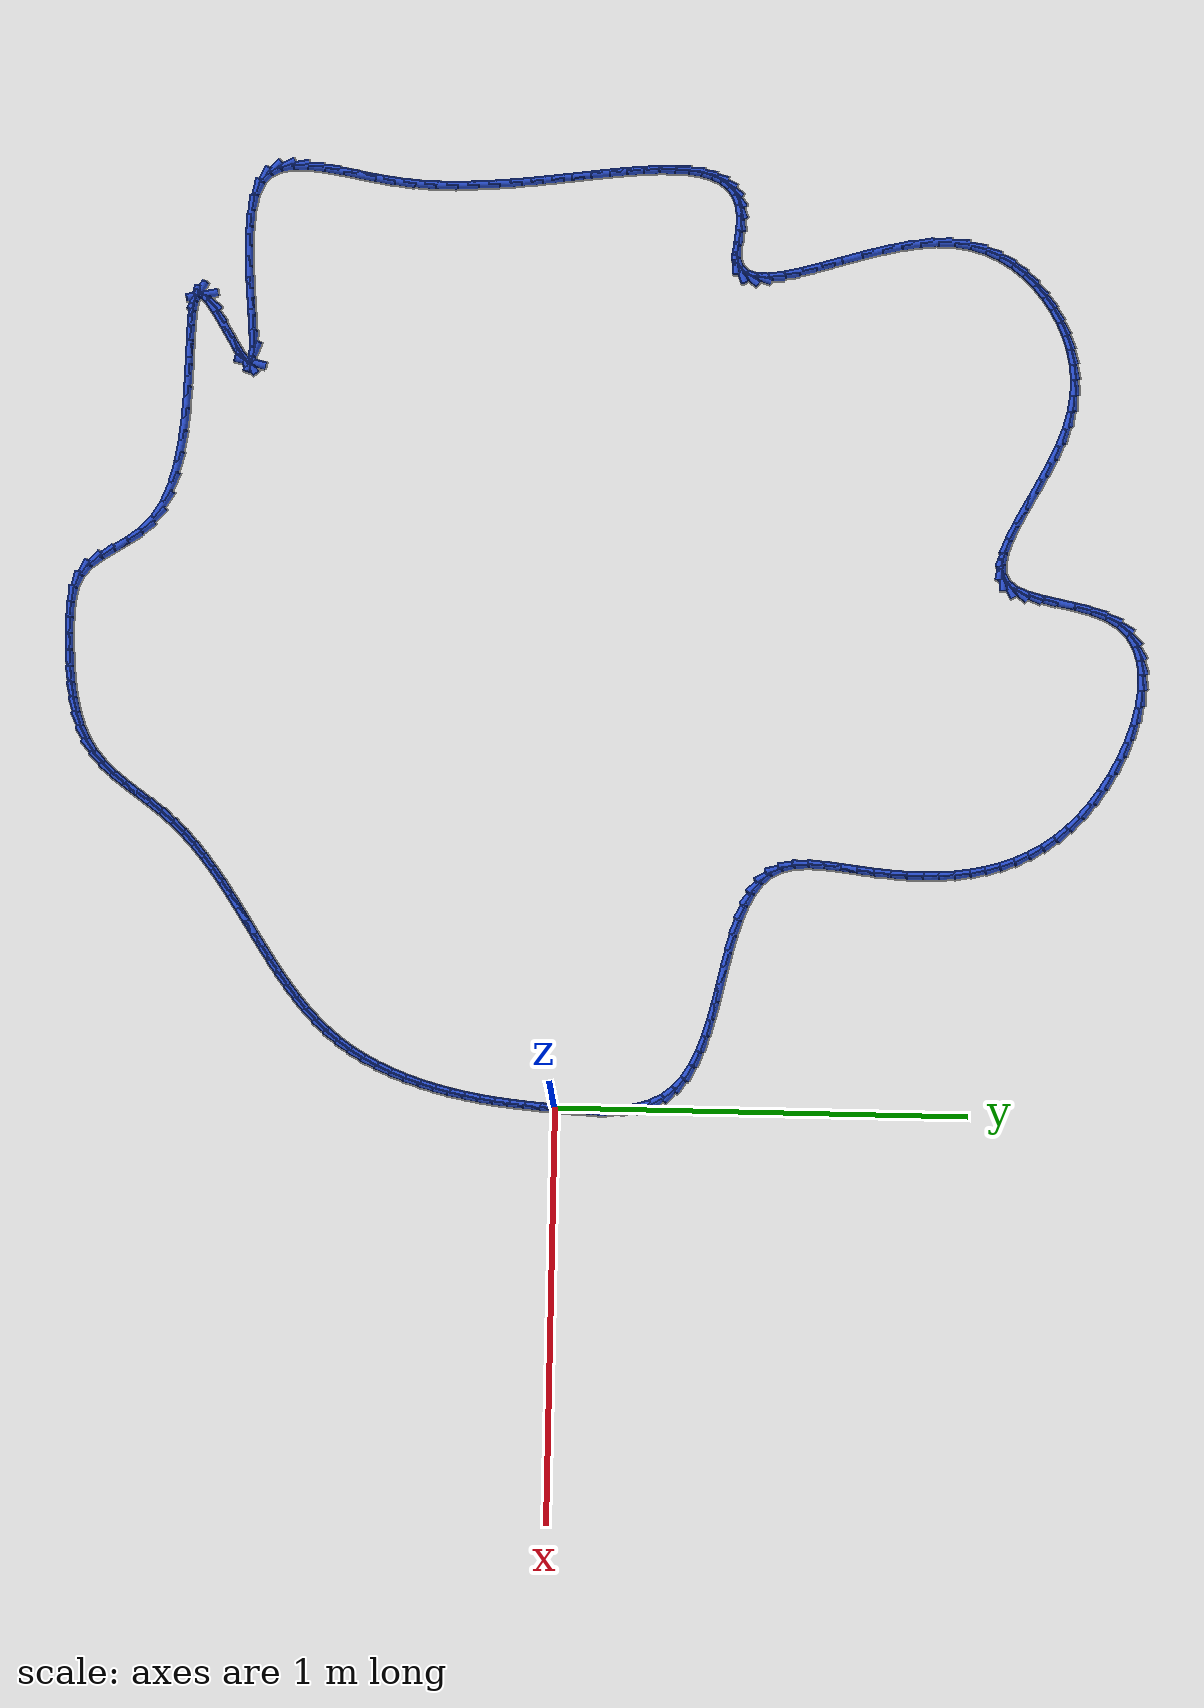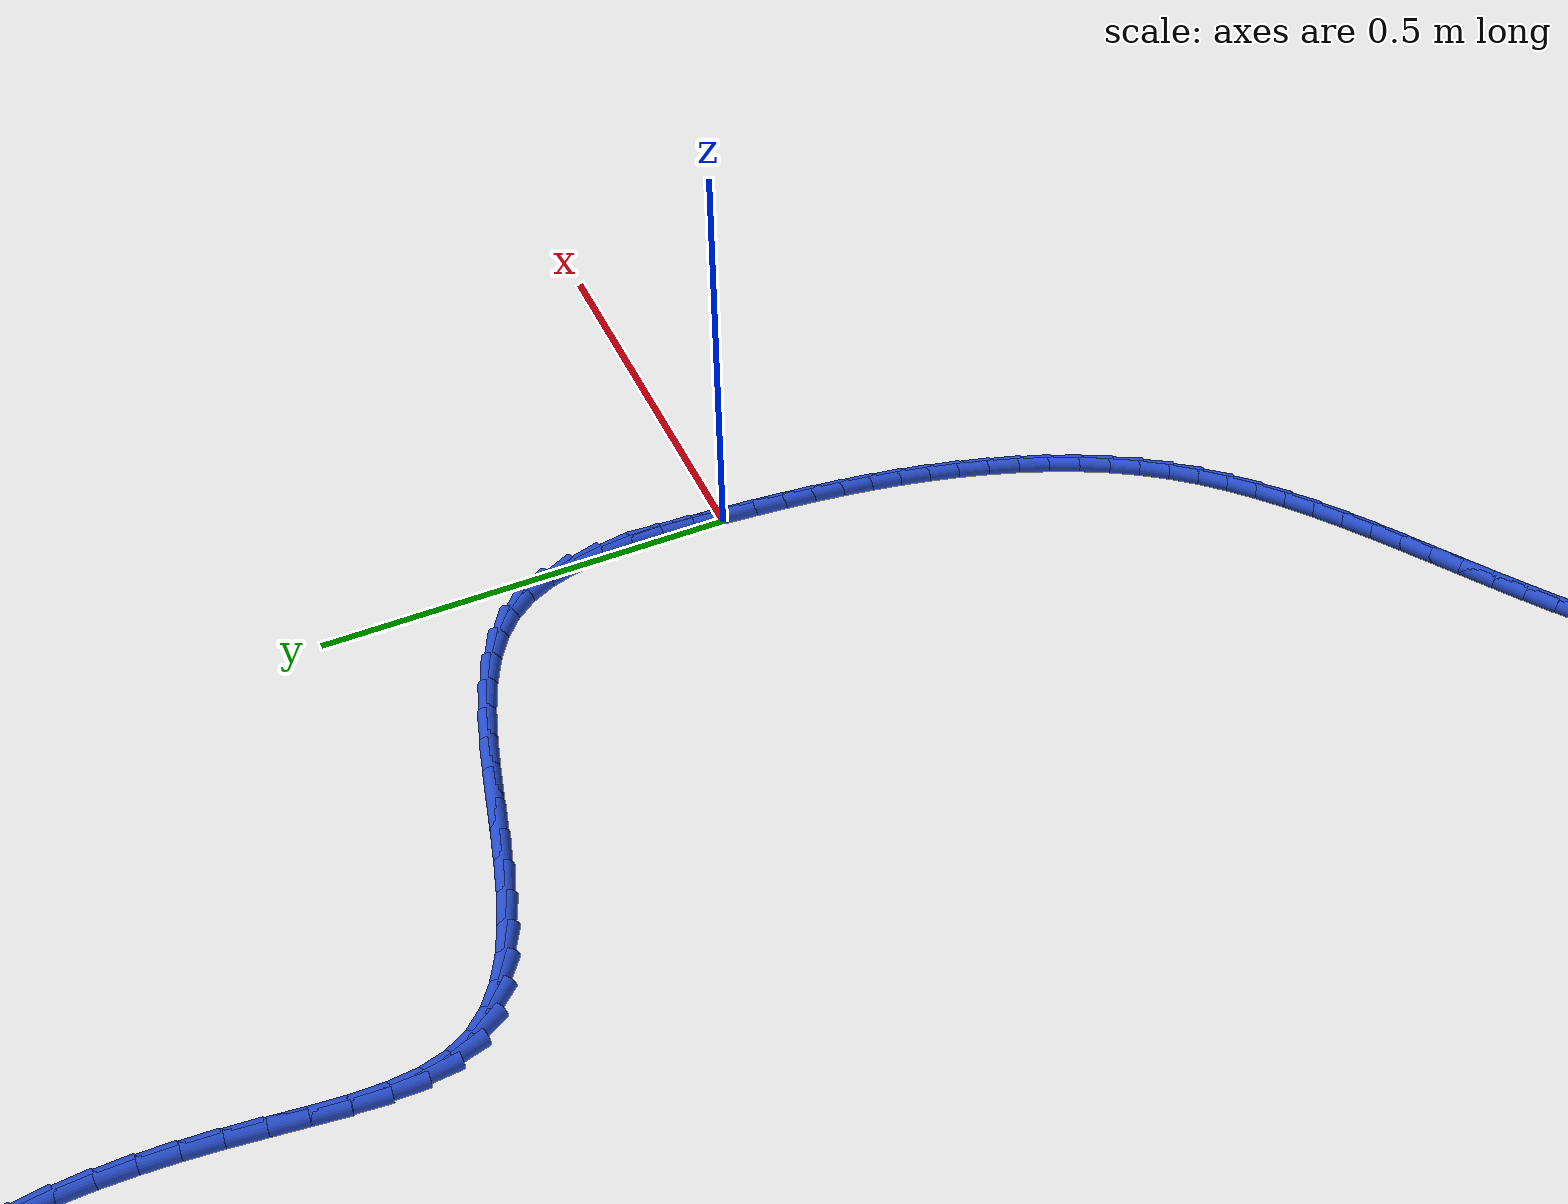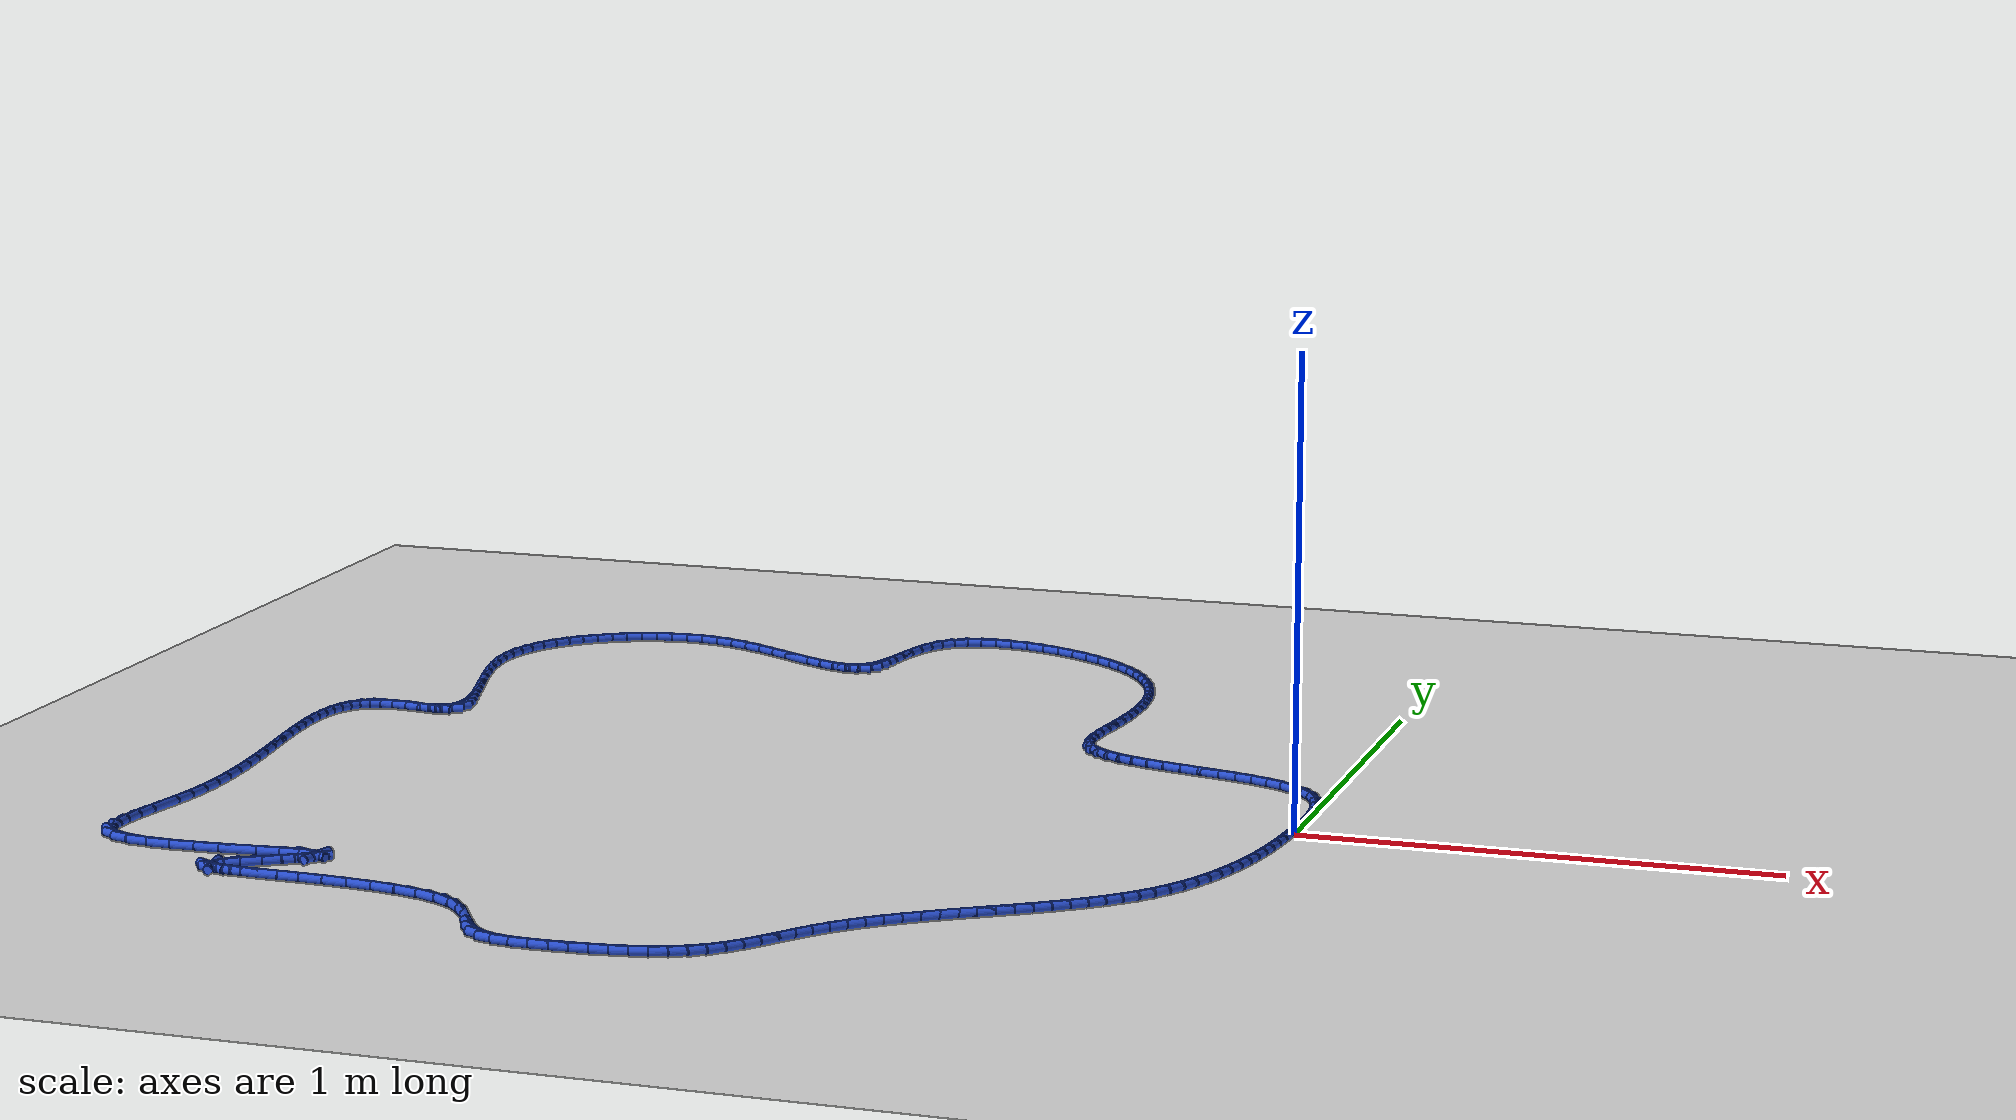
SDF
<sdf version="1.6">
 <world name="default">
  <light name="sun" type="directional">
   <pose>0 0 10 0 -0 0</pose>
   <diffuse>0.8 0.8 0.8 1</diffuse>
   <specular>0.2 0.2 0.2 1</specular>
   <attenuation>
    <range>1000</range>
    <constant>0.9</constant>
    <linear>0.01</linear>
    <quadratic>0.001</quadratic>
   </attenuation>
   <direction>-0.5 0.1 -0.9</direction>
  </light>
  <model name="ground_plane">
   <static>1</static>
   <link name="link">
    <collision name="collision">
     <geometry><plane><normal>0 0 1</normal><size>100 100</size></plane></geometry>
     <surface><friction><ode><mu>100</mu><mu2>50</mu2></ode></friction></surface>
    </collision>
    <visual name="visual">
     <cast_shadows>0</cast_shadows>
     <geometry><plane><normal>0 0 1</normal><size>100 100</size></plane></geometry>
     <material>
      <script><uri>file://media/materials/scripts/gazebo.material</uri><name>Gazebo/WhiteGlow</name></script>
     </material>
    </visual>
   </link>
  </model>
  <gravity>0 0 -9.8</gravity>
  <magnetic_field>6e-06 2.3e-05 -4.2e-05</magnetic_field>
  <atmosphere type="adiabatic"/>
  <physics name="default_physics" default="0" type="ode">
   <max_step_size>0.001</max_step_size>
   <real_time_factor>1</real_time_factor>
   <real_time_update_rate>1000</real_time_update_rate>
  </physics>
  <scene><ambient>0.4 0.4 0.4 1</ambient><background>0.7 0.7 0.7 1</background><shadows>1</shadows></scene>
  <spherical_coordinates>
   <surface_model>EARTH_WGS84</surface_model>
   <latitude_deg>0</latitude_deg>
   <longitude_deg>0</longitude_deg>
   <elevation>0</elevation>
   <heading_deg>0</heading_deg>
  </spherical_coordinates>
  <model name="line">
   <link name="link_0">
    <pose>-2.0383000842727483e-17 -6.938893903907228e-17 0.01 0 1.57 1.5079676238680595</pose>
    <collision name="collision">
     <geometry><cylinder><radius>0.01</radius><length>0.08</length></cylinder></geometry>
    </collision>
    <visual name="visual">
     <material>
      <script><name>Gazebo/Blue</name><uri>file://media/materials/scripts/gazebo.material</uri></script>
     </material>
     <geometry><cylinder><radius>0.01</radius><length>0.08</length></cylinder></geometry>
    </visual>
   </link>
   <link name="link_1">
    <pose>0.002503821656769798 0.039799106238007725 0.01 0 1.57 1.5336063342336432</pose>
    <collision name="collision">
     <geometry><cylinder><radius>0.01</radius><length>0.08</length></cylinder></geometry>
    </collision>
    <visual name="visual">
     <material>
      <script><name>Gazebo/Blue</name><uri>file://media/materials/scripts/gazebo.material</uri></script>
     </material>
     <geometry><cylinder><radius>0.01</radius><length>0.08</length></cylinder></geometry>
    </visual>
   </link>
   <link name="link_2">
    <pose>0.003999209356199292 0.07998997780202757 0.01 0 1.57 -1.5634955819797465</pose>
    <collision name="collision">
     <geometry><cylinder><radius>0.01</radius><length>0.08</length></cylinder></geometry>
    </collision>
    <visual name="visual">
     <material>
      <script><name>Gazebo/Blue</name><uri>file://media/materials/scripts/gazebo.material</uri></script>
     </material>
     <geometry><cylinder><radius>0.01</radius><length>0.08</length></cylinder></geometry>
    </visual>
   </link>
   <link name="link_3">
    <pose>0.0037084110090023084 0.11982059617579742 0.01 0 1.57 -1.497198652115567</pose>
    <collision name="collision">
     <geometry><cylinder><radius>0.01</radius><length>0.08</length></cylinder></geometry>
    </collision>
    <visual name="visual">
     <material>
      <script><name>Gazebo/Blue</name><uri>file://media/materials/scripts/gazebo.material</uri></script>
     </material>
     <geometry><cylinder><radius>0.01</radius><length>0.08</length></cylinder></geometry>
    </visual>
   </link>
   <link name="link_4">
    <pose>0.0008536745258926979 0.15853894284305514 0.01 0 1.57 -1.4042201353368124</pose>
    <collision name="collision">
     <geometry><cylinder><radius>0.01</radius><length>0.08</length></cylinder></geometry>
    </collision>
    <visual name="visual">
     <material>
      <script><name>Gazebo/Blue</name><uri>file://media/materials/scripts/gazebo.material</uri></script>
     </material>
     <geometry><cylinder><radius>0.01</radius><length>0.08</length></cylinder></geometry>
    </visual>
   </link>
   <link name="link_5">
    <pose>-0.005342752182415693 0.19539299928753864 0.01 0 1.57 -1.2781463446124195</pose>
    <collision name="collision">
     <geometry><cylinder><radius>0.01</radius><length>0.08</length></cylinder></geometry>
    </collision>
    <visual name="visual">
     <material>
      <script><name>Gazebo/Blue</name><uri>file://media/materials/scripts/gazebo.material</uri></script>
     </material>
     <geometry><cylinder><radius>0.01</radius><length>0.08</length></cylinder></geometry>
    </visual>
   </link>
   <link name="link_6">
    <pose>-0.015658621205209035 0.22963074699298586 0.01 0 1.57 -1.1129093119912399</pose>
    <collision name="collision">
     <geometry><cylinder><radius>0.01</radius><length>0.08</length></cylinder></geometry>
    </collision>
    <visual name="visual">
     <material>
      <script><name>Gazebo/Blue</name><uri>file://media/materials/scripts/gazebo.material</uri></script>
     </material>
     <geometry><cylinder><radius>0.01</radius><length>0.08</length></cylinder></geometry>
    </visual>
   </link>
   <link name="link_7">
    <pose>-0.030871684631773456 0.26050016744313453 0.01 0 1.57 -0.9108062553281792</pose>
    <collision name="collision">
     <geometry><cylinder><radius>0.01</radius><length>0.08</length></cylinder></geometry>
    </collision>
    <visual name="visual">
     <material>
      <script><name>Gazebo/Blue</name><uri>file://media/materials/scripts/gazebo.material</uri></script>
     </material>
     <geometry><cylinder><radius>0.01</radius><length>0.08</length></cylinder></geometry>
    </visual>
   </link>
   <link name="link_8">
    <pose>-0.051681644125258296 0.28731405010835476 0.01 0 1.57 -0.7161671170750653</pose>
    <collision name="collision">
     <geometry><cylinder><radius>0.01</radius><length>0.08</length></cylinder></geometry>
    </collision>
    <visual name="visual">
     <material>
      <script><name>Gazebo/Blue</name><uri>file://media/materials/scripts/gazebo.material</uri></script>
     </material>
     <geometry><cylinder><radius>0.01</radius><length>0.08</length></cylinder></geometry>
    </visual>
   </link>
   <link name="link_9">
    <pose>-0.07789444962671288 0.31012729763539715 0.01 0 1.57 -0.5599707193890993</pose>
    <collision name="collision">
     <geometry><cylinder><radius>0.01</radius><length>0.08</length></cylinder></geometry>
    </collision>
    <visual name="visual">
     <material>
      <script><name>Gazebo/Blue</name><uri>file://media/materials/scripts/gazebo.material</uri></script>
     </material>
     <geometry><cylinder><radius>0.01</radius><length>0.08</length></cylinder></geometry>
    </visual>
   </link>
   <link name="link_10">
    <pose>-0.10874582263680659 0.3294682932011068 0.01 0 1.57 -0.4414363705972254</pose>
    <collision name="collision">
     <geometry><cylinder><radius>0.01</radius><length>0.08</length></cylinder></geometry>
    </collision>
    <visual name="visual">
     <material>
      <script><name>Gazebo/Blue</name><uri>file://media/materials/scripts/gazebo.material</uri></script>
     </material>
     <geometry><cylinder><radius>0.01</radius><length>0.08</length></cylinder></geometry>
    </visual>
   </link>
   <link name="link_11">
    <pose>-0.14346226366210146 0.34587307649482263 0.01 0 1.57 -0.3547438940363277</pose>
    <collision name="collision">
     <geometry><cylinder><radius>0.01</radius><length>0.08</length></cylinder></geometry>
    </collision>
    <visual name="visual">
     <material>
      <script><name>Gazebo/Blue</name><uri>file://media/materials/scripts/gazebo.material</uri></script>
     </material>
     <geometry><cylinder><radius>0.01</radius><length>0.08</length></cylinder></geometry>
    </visual>
   </link>
   <link name="link_12">
    <pose>-0.18127027320915934 0.359877687205883 0.01 0 1.57 -0.2938021960590582</pose>
    <collision name="collision">
     <geometry><cylinder><radius>0.01</radius><length>0.08</length></cylinder></geometry>
    </collision>
    <visual name="visual">
     <material>
      <script><name>Gazebo/Blue</name><uri>file://media/materials/scripts/gazebo.material</uri></script>
     </material>
     <geometry><cylinder><radius>0.01</radius><length>0.08</length></cylinder></geometry>
    </visual>
   </link>
   <link name="link_13">
    <pose>-0.22139635178454212 0.37201816502362717 0.01 0 1.57 -0.2538738371087145</pose>
    <collision name="collision">
     <geometry><cylinder><radius>0.01</radius><length>0.08</length></cylinder></geometry>
    </collision>
    <visual name="visual">
     <material>
      <script><name>Gazebo/Blue</name><uri>file://media/materials/scripts/gazebo.material</uri></script>
     </material>
     <geometry><cylinder><radius>0.01</radius><length>0.08</length></cylinder></geometry>
    </visual>
   </link>
   <link name="link_14">
    <pose>-0.2630669998948117 0.38283054963739377 0.01 0 1.57 -0.23185059781718584</pose>
    <collision name="collision">
     <geometry><cylinder><radius>0.01</radius><length>0.08</length></cylinder></geometry>
    </collision>
    <visual name="visual">
     <material>
      <script><name>Gazebo/Blue</name><uri>file://media/materials/scripts/gazebo.material</uri></script>
     </material>
     <geometry><cylinder><radius>0.01</radius><length>0.08</length></cylinder></geometry>
    </visual>
   </link>
   <link name="link_15">
    <pose>-0.30550871804653 0.3928508807365217 0.01 0 1.57 -0.22614181010170126</pose>
    <collision name="collision">
     <geometry><cylinder><radius>0.01</radius><length>0.08</length></cylinder></geometry>
    </collision>
    <visual name="visual">
     <material>
      <script><name>Gazebo/Blue</name><uri>file://media/materials/scripts/gazebo.material</uri></script>
     </material>
     <geometry><cylinder><radius>0.01</radius><length>0.08</length></cylinder></geometry>
    </visual>
   </link>
   <link name="link_16">
    <pose>-0.3479480067462591 0.4026151980103497 0.01 0 1.57 -0.23656909423214825</pose>
    <collision name="collision">
     <geometry><cylinder><radius>0.01</radius><length>0.08</length></cylinder></geometry>
    </collision>
    <visual name="visual">
     <material>
      <script><name>Gazebo/Blue</name><uri>file://media/materials/scripts/gazebo.material</uri></script>
     </material>
     <geometry><cylinder><radius>0.01</radius><length>0.08</length></cylinder></geometry>
    </visual>
   </link>
   <link name="link_17">
    <pose>-0.3896113665005606 0.41265954114821657 0.01 0 1.57 -0.26440056430822606</pose>
    <collision name="collision">
     <geometry><cylinder><radius>0.01</radius><length>0.08</length></cylinder></geometry>
    </collision>
    <visual name="visual">
     <material>
      <script><name>Gazebo/Blue</name><uri>file://media/materials/scripts/gazebo.material</uri></script>
     </material>
     <geometry><cylinder><radius>0.01</radius><length>0.08</length></cylinder></geometry>
    </visual>
   </link>
   <link name="link_18">
    <pose>-0.4297252978159968 0.4235199498394611 0.01 0 1.57 -0.31256614276419575</pose>
    <collision name="collision">
     <geometry><cylinder><radius>0.01</radius><length>0.08</length></cylinder></geometry>
    </collision>
    <visual name="visual">
     <material>
      <script><name>Gazebo/Blue</name><uri>file://media/materials/scripts/gazebo.material</uri></script>
     </material>
     <geometry><cylinder><radius>0.01</radius><length>0.08</length></cylinder></geometry>
    </visual>
   </link>
   <link name="link_19">
    <pose>-0.4675163011991292 0.43573246377342223 0.01 0 1.57 -0.38603078774481725</pose>
    <collision name="collision">
     <geometry><cylinder><radius>0.01</radius><length>0.08</length></cylinder></geometry>
    </collision>
    <visual name="visual">
     <material>
      <script><name>Gazebo/Blue</name><uri>file://media/materials/scripts/gazebo.material</uri></script>
     </material>
     <geometry><cylinder><radius>0.01</radius><length>0.08</length></cylinder></geometry>
    </visual>
   </link>
   <link name="link_20">
    <pose>-0.50221087715652 0.44983312263943875 0.01 0 1.57 -0.4921025089945729</pose>
    <collision name="collision">
     <geometry><cylinder><radius>0.01</radius><length>0.08</length></cylinder></geometry>
    </collision>
    <visual name="visual">
     <material>
      <script><name>Gazebo/Blue</name><uri>file://media/materials/scripts/gazebo.material</uri></script>
     </material>
     <geometry><cylinder><radius>0.01</radius><length>0.08</length></cylinder></geometry>
    </visual>
   </link>
   <link name="link_21">
    <pose>-0.533035526194731 0.4663579661268493 0.01 0 1.57 -0.6398033910160179</pose>
    <collision name="collision">
     <geometry><cylinder><radius>0.01</radius><length>0.08</length></cylinder></geometry>
    </collision>
    <visual name="visual">
     <material>
      <script><name>Gazebo/Blue</name><uri>file://media/materials/scripts/gazebo.material</uri></script>
     </material>
     <geometry><cylinder><radius>0.01</radius><length>0.08</length></cylinder></geometry>
    </visual>
   </link>
   <link name="link_22">
    <pose>-0.5592167488203241 0.48584303392499284 0.01 0 1.57 -0.8360349913155304</pose>
    <collision name="collision">
     <geometry><cylinder><radius>0.01</radius><length>0.08</length></cylinder></geometry>
    </collision>
    <visual name="visual">
     <material>
      <script><name>Gazebo/Blue</name><uri>file://media/materials/scripts/gazebo.material</uri></script>
     </material>
     <geometry><cylinder><radius>0.01</radius><length>0.08</length></cylinder></geometry>
    </visual>
   </link>
   <link name="link_23">
    <pose>-0.5799810455398614 0.5088243657232083 0.01 0 1.57 -1.0760244658184988</pose>
    <collision name="collision">
     <geometry><cylinder><radius>0.01</radius><length>0.08</length></cylinder></geometry>
    </collision>
    <visual name="visual">
     <material>
      <script><name>Gazebo/Blue</name><uri>file://media/materials/scripts/gazebo.material</uri></script>
     </material>
     <geometry><cylinder><radius>0.01</radius><length>0.08</length></cylinder></geometry>
    </visual>
   </link>
   <link name="link_24">
    <pose>-0.5945555756327332 0.5358375825081924 0.01 0 1.57 -1.3168480507175693</pose>
    <collision name="collision">
     <geometry><cylinder><radius>0.01</radius><length>0.08</length></cylinder></geometry>
    </collision>
    <visual name="visual">
     <material>
      <script><name>Gazebo/Blue</name><uri>file://media/materials/scripts/gazebo.material</uri></script>
     </material>
     <geometry><cylinder><radius>0.01</radius><length>0.08</length></cylinder></geometry>
    </visual>
   </link>
   <link name="link_25">
    <pose>-0.6026695847474297 0.5670991893587395 0.01 0 1.57 -1.4911927266280636</pose>
    <collision name="collision">
     <geometry><cylinder><radius>0.01</radius><length>0.08</length></cylinder></geometry>
    </collision>
    <visual name="visual">
     <material>
      <script><name>Gazebo/Blue</name><uri>file://media/materials/scripts/gazebo.material</uri></script>
     </material>
     <geometry><cylinder><radius>0.01</radius><length>0.08</length></cylinder></geometry>
    </visual>
   </link>
   <link name="link_26">
    <pose>-0.6054487633783233 0.6019381393461524 0.01 0 1.57 1.5391746137286253</pose>
    <collision name="collision">
     <geometry><cylinder><radius>0.01</radius><length>0.08</length></cylinder></geometry>
    </collision>
    <visual name="visual">
     <material>
      <script><name>Gazebo/Blue</name><uri>file://media/materials/scripts/gazebo.material</uri></script>
     </material>
     <geometry><cylinder><radius>0.01</radius><length>0.08</length></cylinder></geometry>
    </visual>
   </link>
   <link name="link_27">
    <pose>-0.6042596380090349 0.6395303150739925 0.01 0 1.57 1.475168354284038</pose>
    <collision name="collision">
     <geometry><cylinder><radius>0.01</radius><length>0.08</length></cylinder></geometry>
    </collision>
    <visual name="visual">
     <material>
      <script><name>Gazebo/Blue</name><uri>file://media/materials/scripts/gazebo.material</uri></script>
     </material>
     <geometry><cylinder><radius>0.01</radius><length>0.08</length></cylinder></geometry>
    </visual>
   </link>
   <link name="link_28">
    <pose>-0.6004687351231859 0.679051599145821 0.01 0 1.57 1.4477049610633939</pose>
    <collision name="collision">
     <geometry><cylinder><radius>0.01</radius><length>0.08</length></cylinder></geometry>
    </collision>
    <visual name="visual">
     <material>
      <script><name>Gazebo/Blue</name><uri>file://media/materials/scripts/gazebo.material</uri></script>
     </material>
     <geometry><cylinder><radius>0.01</radius><length>0.08</length></cylinder></geometry>
    </visual>
   </link>
   <link name="link_29">
    <pose>-0.5954425812043965 0.719677874165199 0.01 0 1.57 1.4516589366826929</pose>
    <collision name="collision">
     <geometry><cylinder><radius>0.01</radius><length>0.08</length></cylinder></geometry>
    </collision>
    <visual name="visual">
     <material>
      <script><name>Gazebo/Blue</name><uri>file://media/materials/scripts/gazebo.material</uri></script>
     </material>
     <geometry><cylinder><radius>0.01</radius><length>0.08</length></cylinder></geometry>
    </visual>
   </link>
   <link name="link_30">
    <pose>-0.590545665910042 0.7605863149088202 0.01 0 1.57 1.4786295311218423</pose>
    <collision name="collision">
     <geometry><cylinder><radius>0.01</radius><length>0.08</length></cylinder></geometry>
    </collision>
    <visual name="visual">
     <material>
      <script><name>Gazebo/Blue</name><uri>file://media/materials/scripts/gazebo.material</uri></script>
     </material>
     <geometry><cylinder><radius>0.01</radius><length>0.08</length></cylinder></geometry>
    </visual>
   </link>
   <link name="link_31">
    <pose>-0.5867940977808205 0.8011751109400964 0.01 0 1.57 1.5128110846705394</pose>
    <collision name="collision">
     <geometry><cylinder><radius>0.01</radius><length>0.08</length></cylinder></geometry>
    </collision>
    <visual name="visual">
     <material>
      <script><name>Gazebo/Blue</name><uri>file://media/materials/scripts/gazebo.material</uri></script>
     </material>
     <geometry><cylinder><radius>0.01</radius><length>0.08</length></cylinder></geometry>
    </visual>
   </link>
   <link name="link_32">
    <pose>-0.5844641498184621 0.8413118073242912 0.01 0 1.57 1.5524554792189942</pose>
    <collision name="collision">
     <geometry><cylinder><radius>0.01</radius><length>0.08</length></cylinder></geometry>
    </collision>
    <visual name="visual">
     <material>
      <script><name>Gazebo/Blue</name><uri>file://media/materials/scripts/gazebo.material</uri></script>
     </material>
     <geometry><cylinder><radius>0.01</radius><length>0.08</length></cylinder></geometry>
    </visual>
   </link>
   <link name="link_33">
    <pose>-0.5837375484400176 0.8809239299701968 0.01 0 1.57 -1.543673168519768</pose>
    <collision name="collision">
     <geometry><cylinder><radius>0.01</radius><length>0.08</length></cylinder></geometry>
    </collision>
    <visual name="visual">
     <material>
      <script><name>Gazebo/Blue</name><uri>file://media/materials/scripts/gazebo.material</uri></script>
     </material>
     <geometry><cylinder><radius>0.01</radius><length>0.08</length></cylinder></geometry>
    </visual>
   </link>
   <link name="link_34">
    <pose>-0.5847960200625375 0.9199390047866061 0.01 0 1.57 -1.4920644451887517</pose>
    <collision name="collision">
     <geometry><cylinder><radius>0.01</radius><length>0.08</length></cylinder></geometry>
    </collision>
    <visual name="visual">
     <material>
      <script><name>Gazebo/Blue</name><uri>file://media/materials/scripts/gazebo.material</uri></script>
     </material>
     <geometry><cylinder><radius>0.01</radius><length>0.08</length></cylinder></geometry>
    </visual>
   </link>
   <link name="link_35">
    <pose>-0.587821291103073 0.9582845576823119 0.01 0 1.57 -1.4340668323699233</pose>
    <collision name="collision">
     <geometry><cylinder><radius>0.01</radius><length>0.08</length></cylinder></geometry>
    </collision>
    <visual name="visual">
     <material>
      <script><name>Gazebo/Blue</name><uri>file://media/materials/scripts/gazebo.material</uri></script>
     </material>
     <geometry><cylinder><radius>0.01</radius><length>0.08</length></cylinder></geometry>
    </visual>
   </link>
   <link name="link_36">
    <pose>-0.5929950879786746 0.9958881145661065 0.01 0 1.57 -1.3695817161351025</pose>
    <collision name="collision">
     <geometry><cylinder><radius>0.01</radius><length>0.08</length></cylinder></geometry>
    </collision>
    <visual name="visual">
     <material>
      <script><name>Gazebo/Blue</name><uri>file://media/materials/scripts/gazebo.material</uri></script>
     </material>
     <geometry><cylinder><radius>0.01</radius><length>0.08</length></cylinder></geometry>
    </visual>
   </link>
   <link name="link_37">
    <pose>-0.6004991371063935 1.0326772013467829 0.01 0 1.57 -1.2987324777566824</pose>
    <collision name="collision">
     <geometry><cylinder><radius>0.01</radius><length>0.08</length></cylinder></geometry>
    </collision>
    <visual name="visual">
     <material>
      <script><name>Gazebo/Blue</name><uri>file://media/materials/scripts/gazebo.material</uri></script>
     </material>
     <geometry><cylinder><radius>0.01</radius><length>0.08</length></cylinder></geometry>
    </visual>
   </link>
   <link name="link_38">
    <pose>-0.61051516490328 1.0685793439331328 0.01 0 1.57 -1.2219422263099349</pose>
    <collision name="collision">
     <geometry><cylinder><radius>0.01</radius><length>0.08</length></cylinder></geometry>
    </collision>
    <visual name="visual">
     <material>
      <script><name>Gazebo/Blue</name><uri>file://media/materials/scripts/gazebo.material</uri></script>
     </material>
     <geometry><cylinder><radius>0.01</radius><length>0.08</length></cylinder></geometry>
    </visual>
   </link>
   <link name="link_39">
    <pose>-0.6232248977863851 1.10352206823395 0.01 0 1.57 -1.1399939613351844</pose>
    <collision name="collision">
     <geometry><cylinder><radius>0.01</radius><length>0.08</length></cylinder></geometry>
    </collision>
    <visual name="visual">
     <material>
      <script><name>Gazebo/Blue</name><uri>file://media/materials/scripts/gazebo.material</uri></script>
     </material>
     <geometry><cylinder><radius>0.01</radius><length>0.08</length></cylinder></geometry>
    </visual>
   </link>
   <link name="link_40">
    <pose>-0.6388100621727599 1.137432900158027 0.01 0 1.57 -1.054048534012462</pose>
    <collision name="collision">
     <geometry><cylinder><radius>0.01</radius><length>0.08</length></cylinder></geometry>
    </collision>
    <visual name="visual">
     <material>
      <script><name>Gazebo/Blue</name><uri>file://media/materials/scripts/gazebo.material</uri></script>
     </material>
     <geometry><cylinder><radius>0.01</radius><length>0.08</length></cylinder></geometry>
    </visual>
   </link>
   <link name="link_41">
    <pose>-0.6574523844794549 1.1702393656141554 0.01 0 1.57 -0.9655985340125656</pose>
    <collision name="collision">
     <geometry><cylinder><radius>0.01</radius><length>0.08</length></cylinder></geometry>
    </collision>
    <visual name="visual">
     <material>
      <script><name>Gazebo/Blue</name><uri>file://media/materials/scripts/gazebo.material</uri></script>
     </material>
     <geometry><cylinder><radius>0.01</radius><length>0.08</length></cylinder></geometry>
    </visual>
   </link>
   <link name="link_42">
    <pose>-0.6793335911235211 1.201868990511129 0.01 0 1.57 -0.876351604667606</pose>
    <collision name="collision">
     <geometry><cylinder><radius>0.01</radius><length>0.08</length></cylinder></geometry>
    </collision>
    <visual name="visual">
     <material>
      <script><name>Gazebo/Blue</name><uri>file://media/materials/scripts/gazebo.material</uri></script>
     </material>
     <geometry><cylinder><radius>0.01</radius><length>0.08</length></cylinder></geometry>
    </visual>
   </link>
   <link name="link_43">
    <pose>-0.7046354085220089 1.2322493007577395 0.01 0 1.57 -0.7880613698015566</pose>
    <collision name="collision">
     <geometry><cylinder><radius>0.01</radius><length>0.08</length></cylinder></geometry>
    </collision>
    <visual name="visual">
     <material>
      <script><name>Gazebo/Blue</name><uri>file://media/materials/scripts/gazebo.material</uri></script>
     </material>
     <geometry><cylinder><radius>0.01</radius><length>0.08</length></cylinder></geometry>
    </visual>
   </link>
   <link name="link_44">
    <pose>-0.7335395630919697 1.2613078222627805 0.01 0 1.57 -0.7024722750563569</pose>
    <collision name="collision">
     <geometry><cylinder><radius>0.01</radius><length>0.08</length></cylinder></geometry>
    </collision>
    <visual name="visual">
     <material>
      <script><name>Gazebo/Blue</name><uri>file://media/materials/scripts/gazebo.material</uri></script>
     </material>
     <geometry><cylinder><radius>0.01</radius><length>0.08</length></cylinder></geometry>
    </visual>
   </link>
   <link name="link_45">
    <pose>-0.766210639938338 1.288964654555795 0.01 0 1.57 -0.6230756304661877</pose>
    <collision name="collision">
     <geometry><cylinder><radius>0.01</radius><length>0.08</length></cylinder></geometry>
    </collision>
    <visual name="visual">
     <material>
      <script><name>Gazebo/Blue</name><uri>file://media/materials/scripts/gazebo.material</uri></script>
     </material>
     <geometry><cylinder><radius>0.01</radius><length>0.08</length></cylinder></geometry>
    </visual>
   </link>
   <link name="link_46">
    <pose>-0.8023716161867794 1.3149485729368022 0.01 0 1.57 -0.5496998231448647</pose>
    <collision name="collision">
     <geometry><cylinder><radius>0.01</radius><length>0.08</length></cylinder></geometry>
    </collision>
    <visual name="visual">
     <material>
      <script><name>Gazebo/Blue</name><uri>file://media/materials/scripts/gazebo.material</uri></script>
     </material>
     <geometry><cylinder><radius>0.01</radius><length>0.08</length></cylinder></geometry>
    </visual>
   </link>
   <link name="link_47">
    <pose>-0.8412758296755972 1.3387848840661558 0.01 0 1.57 -0.4785092494315749</pose>
    <collision name="collision">
     <geometry><cylinder><radius>0.01</radius><length>0.08</length></cylinder></geometry>
    </collision>
    <visual name="visual">
     <material>
      <script><name>Gazebo/Blue</name><uri>file://media/materials/scripts/gazebo.material</uri></script>
     </material>
     <geometry><cylinder><radius>0.01</radius><length>0.08</length></cylinder></geometry>
    </visual>
   </link>
   <link name="link_48">
    <pose>-0.8821538640122243 1.359989036458762 0.01 0 1.57 -0.40593747862610907</pose>
    <collision name="collision">
     <geometry><cylinder><radius>0.01</radius><length>0.08</length></cylinder></geometry>
    </collision>
    <visual name="visual">
     <material>
      <script><name>Gazebo/Blue</name><uri>file://media/materials/scripts/gazebo.material</uri></script>
     </material>
     <geometry><cylinder><radius>0.01</radius><length>0.08</length></cylinder></geometry>
    </visual>
   </link>
   <link name="link_49">
    <pose>-0.9242363028040939 1.3780764786295279 0.01 0 1.57 -0.32837622999600635</pose>
    <collision name="collision">
     <geometry><cylinder><radius>0.01</radius><length>0.08</length></cylinder></geometry>
    </collision>
    <visual name="visual">
     <material>
      <script><name>Gazebo/Blue</name><uri>file://media/materials/scripts/gazebo.material</uri></script>
     </material>
     <geometry><cylinder><radius>0.01</radius><length>0.08</length></cylinder></geometry>
    </visual>
   </link>
   <link name="link_50">
    <pose>-0.9667537296586401 1.3925626590933604 0.01 0 1.57 -0.2417323072473185</pose>
    <collision name="collision">
     <geometry><cylinder><radius>0.01</radius><length>0.08</length></cylinder></geometry>
    </collision>
    <visual name="visual">
     <material>
      <script><name>Gazebo/Blue</name><uri>file://media/materials/scripts/gazebo.material</uri></script>
     </material>
     <geometry><cylinder><radius>0.01</radius><length>0.08</length></cylinder></geometry>
    </visual>
   </link>
   <link name="link_51">
    <pose>-1.008936728183296 1.4029630263651662 0.01 0 1.57 -0.14097970569885052</pose>
    <collision name="collision">
     <geometry><cylinder><radius>0.01</radius><length>0.08</length></cylinder></geometry>
    </collision>
    <visual name="visual">
     <material>
      <script><name>Gazebo/Blue</name><uri>file://media/materials/scripts/gazebo.material</uri></script>
     </material>
     <geometry><cylinder><radius>0.01</radius><length>0.08</length></cylinder></geometry>
    </visual>
   </link>
   <link name="link_52">
    <pose>-1.0500158819854946 1.4087930289598525 0.01 0 1.57 -0.019767066252055987</pose>
    <collision name="collision">
     <geometry><cylinder><radius>0.01</radius><length>0.08</length></cylinder></geometry>
    </collision>
    <visual name="visual">
     <material>
      <script><name>Gazebo/Blue</name><uri>file://media/materials/scripts/gazebo.material</uri></script>
     </material>
     <geometry><cylinder><radius>0.01</radius><length>0.08</length></cylinder></geometry>
    </visual>
   </link>
   <link name="link_53">
    <pose>-1.0892217746726696 1.409568115392326 0.01 0 1.57 0.1295752317281121</pose>
    <collision name="collision">
     <geometry><cylinder><radius>0.01</radius><length>0.08</length></cylinder></geometry>
    </collision>
    <visual name="visual">
     <material>
      <script><name>Gazebo/Blue</name><uri>file://media/materials/scripts/gazebo.material</uri></script>
     </material>
     <geometry><cylinder><radius>0.01</radius><length>0.08</length></cylinder></geometry>
    </visual>
   </link>
   <link name="link_54">
    <pose>-1.1257849898522538 1.4048037341774937 0.01 0 1.57 0.31462161438430297</pose>
    <collision name="collision">
     <geometry><cylinder><radius>0.01</radius><length>0.08</length></cylinder></geometry>
    </collision>
    <visual name="visual">
     <material>
      <script><name>Gazebo/Blue</name><uri>file://media/materials/scripts/gazebo.material</uri></script>
     </material>
     <geometry><cylinder><radius>0.01</radius><length>0.08</length></cylinder></geometry>
    </visual>
   </link>
   <link name="link_55">
    <pose>-1.1589361111316814 1.3940153338302628 0.01 0 1.57 0.538264474833401</pose>
    <collision name="collision">
     <geometry><cylinder><radius>0.01</radius><length>0.08</length></cylinder></geometry>
    </collision>
    <visual name="visual">
     <material>
      <script><name>Gazebo/Blue</name><uri>file://media/materials/scripts/gazebo.material</uri></script>
     </material>
     <geometry><cylinder><radius>0.01</radius><length>0.08</length></cylinder></geometry>
    </visual>
   </link>
   <link name="link_56">
    <pose>-1.1879057221183846 1.376718362865539 0.01 0 1.57 0.7910163124197807</pose>
    <collision name="collision">
     <geometry><cylinder><radius>0.01</radius><length>0.08</length></cylinder></geometry>
    </collision>
    <visual name="visual">
     <material>
      <script><name>Gazebo/Blue</name><uri>file://media/materials/scripts/gazebo.material</uri></script>
     </material>
     <geometry><cylinder><radius>0.01</radius><length>0.08</length></cylinder></geometry>
    </visual>
   </link>
   <link name="link_57">
    <pose>-1.2119244064197976 1.3524282697982302 0.01 0 1.57 1.0406040182301841</pose>
    <collision name="collision">
     <geometry><cylinder><radius>0.01</radius><length>0.08</length></cylinder></geometry>
    </collision>
    <visual name="visual">
     <material>
      <script><name>Gazebo/Blue</name><uri>file://media/materials/scripts/gazebo.material</uri></script>
     </material>
     <geometry><cylinder><radius>0.01</radius><length>0.08</length></cylinder></geometry>
    </visual>
   </link>
   <link name="link_58">
    <pose>-1.2304061120478067 1.3208989586269257 0.01 0 1.57 1.2165703795871112</pose>
    <collision name="collision">
     <geometry><cylinder><radius>0.01</radius><length>0.08</length></cylinder></geometry>
    </collision>
    <visual name="visual">
     <material>
      <script><name>Gazebo/Blue</name><uri>file://media/materials/scripts/gazebo.material</uri></script>
     </material>
     <geometry><cylinder><radius>0.01</radius><length>0.08</length></cylinder></geometry>
    </visual>
   </link>
   <link name="link_59">
    <pose>-1.2441624877663373 1.2837019675298964 0.01 0 1.57 1.3171798967521018</pose>
    <collision name="collision">
     <geometry><cylinder><radius>0.01</radius><length>0.08</length></cylinder></geometry>
    </collision>
    <visual name="visual">
     <material>
      <script><name>Gazebo/Blue</name><uri>file://media/materials/scripts/gazebo.material</uri></script>
     </material>
     <geometry><cylinder><radius>0.01</radius><length>0.08</length></cylinder></geometry>
    </visual>
   </link>
   <link name="link_60">
    <pose>-1.2546486711285703 1.2432456570280275 0.01 0 1.57 1.3637820003790322</pose>
    <collision name="collision">
     <geometry><cylinder><radius>0.01</radius><length>0.08</length></cylinder></geometry>
    </collision>
    <visual name="visual">
     <material>
      <script><name>Gazebo/Blue</name><uri>file://media/materials/scripts/gazebo.material</uri></script>
     </material>
     <geometry><cylinder><radius>0.01</radius><length>0.08</length></cylinder></geometry>
    </visual>
   </link>
   <link name="link_61">
    <pose>-1.2633232184867444 1.2019428336053393 0.01 0 1.57 1.3643634696790135</pose>
    <collision name="collision">
     <geometry><cylinder><radius>0.01</radius><length>0.08</length></cylinder></geometry>
    </collision>
    <visual name="visual">
     <material>
      <script><name>Gazebo/Blue</name><uri>file://media/materials/scripts/gazebo.material</uri></script>
     </material>
     <geometry><cylinder><radius>0.01</radius><length>0.08</length></cylinder></geometry>
    </visual>
   </link>
   <link name="link_62">
    <pose>-1.2716446861930983 1.1622063037458545 0.01 0 1.57 1.3130255601070009</pose>
    <collision name="collision">
     <geometry><cylinder><radius>0.01</radius><length>0.08</length></cylinder></geometry>
    </collision>
    <visual name="visual">
     <material>
      <script><name>Gazebo/Blue</name><uri>file://media/materials/scripts/gazebo.material</uri></script>
     </material>
     <geometry><cylinder><radius>0.01</radius><length>0.08</length></cylinder></geometry>
    </visual>
   </link>
   <link name="link_63">
    <pose>-1.2810716305998713 1.1264488739335936 0.01 0 1.57 1.1831251299141767</pose>
    <collision name="collision">
     <geometry><cylinder><radius>0.01</radius><length>0.08</length></cylinder></geometry>
    </collision>
    <visual name="visual">
     <material>
      <script><name>Gazebo/Blue</name><uri>file://media/materials/scripts/gazebo.material</uri></script>
     </material>
     <geometry><cylinder><radius>0.01</radius><length>0.08</length></cylinder></geometry>
    </visual>
   </link>
   <link name="link_64">
    <pose>-1.293062608059302 1.0970833506525801 0.01 0 1.57 0.9095397740615421</pose>
    <collision name="collision">
     <geometry><cylinder><radius>0.01</radius><length>0.08</length></cylinder></geometry>
    </collision>
    <visual name="visual">
     <material>
      <script><name>Gazebo/Blue</name><uri>file://media/materials/scripts/gazebo.material</uri></script>
     </material>
     <geometry><cylinder><radius>0.01</radius><length>0.08</length></cylinder></geometry>
    </visual>
   </link>
   <link name="link_65">
    <pose>-1.3090702495008555 1.0765111571392236 0.01 0 1.57 0.4706465247583107</pose>
    <collision name="collision">
     <geometry><cylinder><radius>0.01</radius><length>0.08</length></cylinder></geometry>
    </collision>
    <visual name="visual">
     <material>
      <script><name>Gazebo/Blue</name><uri>file://media/materials/scripts/gazebo.material</uri></script>
     </material>
     <geometry><cylinder><radius>0.01</radius><length>0.08</length></cylinder></geometry>
    </visual>
   </link>
   <link name="link_66">
    <pose>-1.3299094614297704 1.065908593072264 0.01 0 1.57 0.0694172365579332</pose>
    <collision name="collision">
     <geometry><cylinder><radius>0.01</radius><length>0.08</length></cylinder></geometry>
    </collision>
    <visual name="visual">
     <material>
      <script><name>Gazebo/Blue</name><uri>file://media/materials/scripts/gazebo.material</uri></script>
     </material>
     <geometry><cylinder><radius>0.01</radius><length>0.08</length></cylinder></geometry>
    </visual>
   </link>
   <link name="link_67">
    <pose>-1.3551970848452408 1.0641503710822984 0.01 0 1.57 -0.19287661218664895</pose>
    <collision name="collision">
     <geometry><cylinder><radius>0.01</radius><length>0.08</length></cylinder></geometry>
    </collision>
    <visual name="visual">
     <material>
      <script><name>Gazebo/Blue</name><uri>file://media/materials/scripts/gazebo.material</uri></script>
     </material>
     <geometry><cylinder><radius>0.01</radius><length>0.08</length></cylinder></geometry>
    </visual>
   </link>
   <link name="link_68">
    <pose>-1.384417798149253 1.069857308065134 0.01 0 1.57 -0.34672301196957256</pose>
    <collision name="collision">
     <geometry><cylinder><radius>0.01</radius><length>0.08</length></cylinder></geometry>
    </collision>
    <visual name="visual">
     <material>
      <script><name>Gazebo/Blue</name><uri>file://media/materials/scripts/gazebo.material</uri></script>
     </material>
     <geometry><cylinder><radius>0.01</radius><length>0.08</length></cylinder></geometry>
    </visual>
   </link>
   <link name="link_69">
    <pose>-1.4170562797437918 1.0816502209165775 0.01 0 1.57 -0.43463689084163853</pose>
    <collision name="collision">
     <geometry><cylinder><radius>0.01</radius><length>0.08</length></cylinder></geometry>
    </collision>
    <visual name="visual">
     <material>
      <script><name>Gazebo/Blue</name><uri>file://media/materials/scripts/gazebo.material</uri></script>
     </material>
     <geometry><cylinder><radius>0.01</radius><length>0.08</length></cylinder></geometry>
    </visual>
   </link>
   <link name="link_70">
    <pose>-1.4525972080308454 1.0981499265324375 0.01 0 1.57 -0.48169033545354895</pose>
    <collision name="collision">
     <geometry><cylinder><radius>0.01</radius><length>0.08</length></cylinder></geometry>
    </collision>
    <visual name="visual">
     <material>
      <script><name>Gazebo/Blue</name><uri>file://media/materials/scripts/gazebo.material</uri></script>
     </material>
     <geometry><cylinder><radius>0.01</radius><length>0.08</length></cylinder></geometry>
    </visual>
   </link>
   <link name="link_71">
    <pose>-1.490525261412398 1.1179772418085203 0.01 0 1.57 -0.500637978189173</pose>
    <collision name="collision">
     <geometry><cylinder><radius>0.01</radius><length>0.08</length></cylinder></geometry>
    </collision>
    <visual name="visual">
     <material>
      <script><name>Gazebo/Blue</name><uri>file://media/materials/scripts/gazebo.material</uri></script>
     </material>
     <geometry><cylinder><radius>0.01</radius><length>0.08</length></cylinder></geometry>
    </visual>
   </link>
   <link name="link_72">
    <pose>-1.5303251182904374 1.139752983640634 0.01 0 1.57 -0.49739850546302883</pose>
    <collision name="collision">
     <geometry><cylinder><radius>0.01</radius><length>0.08</length></cylinder></geometry>
    </collision>
    <visual name="visual">
     <material>
      <script><name>Gazebo/Blue</name><uri>file://media/materials/scripts/gazebo.material</uri></script>
     </material>
     <geometry><cylinder><radius>0.01</radius><length>0.08</length></cylinder></geometry>
    </visual>
   </link>
   <link name="link_73">
    <pose>-1.5714814570669482 1.1620979689245847 0.01 0 1.57 -0.47381111519954383</pose>
    <collision name="collision">
     <geometry><cylinder><radius>0.01</radius><length>0.08</length></cylinder></geometry>
    </collision>
    <visual name="visual">
     <material>
      <script><name>Gazebo/Blue</name><uri>file://media/materials/scripts/gazebo.material</uri></script>
     </material>
     <geometry><cylinder><radius>0.01</radius><length>0.08</length></cylinder></geometry>
    </visual>
   </link>
   <link name="link_74">
    <pose>-1.6134789561439178 1.1836330145561809 0.01 0 1.57 -0.42874111548506816</pose>
    <collision name="collision">
     <geometry><cylinder><radius>0.01</radius><length>0.08</length></cylinder></geometry>
    </collision>
    <visual name="visual">
     <material>
      <script><name>Gazebo/Blue</name><uri>file://media/materials/scripts/gazebo.material</uri></script>
     </material>
     <geometry><cylinder><radius>0.01</radius><length>0.08</length></cylinder></geometry>
    </visual>
   </link>
   <link name="link_75">
    <pose>-1.6558022939233306 1.202978937431229 0.01 0 1.57 -0.35830077747708283</pose>
    <collision name="collision">
     <geometry><cylinder><radius>0.01</radius><length>0.08</length></cylinder></geometry>
    </collision>
    <visual name="visual">
     <material>
      <script><name>Gazebo/Blue</name><uri>file://media/materials/scripts/gazebo.material</uri></script>
     </material>
     <geometry><cylinder><radius>0.01</radius><length>0.08</length></cylinder></geometry>
    </visual>
   </link>
   <link name="link_76">
    <pose>-1.6979361488071745 1.2187565544455368 0.01 0 1.57 -0.2584077429415375</pose>
    <collision name="collision">
     <geometry><cylinder><radius>0.01</radius><length>0.08</length></cylinder></geometry>
    </collision>
    <visual name="visual">
     <material>
      <script><name>Gazebo/Blue</name><uri>file://media/materials/scripts/gazebo.material</uri></script>
     </material>
     <geometry><cylinder><radius>0.01</radius><length>0.08</length></cylinder></geometry>
    </visual>
   </link>
   <link name="link_77">
    <pose>-1.73939469624492 1.2297147668068893 0.01 0 1.57 -0.14523502870412947</pose>
    <collision name="collision">
     <geometry><cylinder><radius>0.01</radius><length>0.08</length></cylinder></geometry>
    </collision>
    <visual name="visual">
     <material>
      <script><name>Gazebo/Blue</name><uri>file://media/materials/scripts/gazebo.material</uri></script>
     </material>
     <geometry><cylinder><radius>0.01</radius><length>0.08</length></cylinder></geometry>
    </visual>
   </link>
   <link name="link_78">
    <pose>-1.779931955581645 1.2356439440383749 0.01 0 1.57 -0.030309355430132568</pose>
    <collision name="collision">
     <geometry><cylinder><radius>0.01</radius><length>0.08</length></cylinder></geometry>
    </collision>
    <visual name="visual">
     <material>
      <script><name>Gazebo/Blue</name><uri>file://media/materials/scripts/gazebo.material</uri></script>
     </material>
     <geometry><cylinder><radius>0.01</radius><length>0.08</length></cylinder></geometry>
    </visual>
   </link>
   <link name="link_79">
    <pose>-1.8194186293638794 1.2368411262912111 0.01 0 1.57 0.08423241091682816</pose>
    <collision name="collision">
     <geometry><cylinder><radius>0.01</radius><length>0.08</length></cylinder></geometry>
    </collision>
    <visual name="visual">
     <material>
      <script><name>Gazebo/Blue</name><uri>file://media/materials/scripts/gazebo.material</uri></script>
     </material>
     <geometry><cylinder><radius>0.01</radius><length>0.08</length></cylinder></geometry>
    </visual>
   </link>
   <link name="link_80">
    <pose>-1.8577261986680003 1.2336067343078492 0.01 0 1.57 0.19650029187158013</pose>
    <collision name="collision">
     <geometry><cylinder><radius>0.01</radius><length>0.08</length></cylinder></geometry>
    </collision>
    <visual name="visual">
     <material>
      <script><name>Gazebo/Blue</name><uri>file://media/materials/scripts/gazebo.material</uri></script>
     </material>
     <geometry><cylinder><radius>0.01</radius><length>0.08</length></cylinder></geometry>
    </visual>
   </link>
   <link name="link_81">
    <pose>-1.8947261445703885 1.2262411888307407 0.01 0 1.57 0.30499915164944663</pose>
    <collision name="collision">
     <geometry><cylinder><radius>0.01</radius><length>0.08</length></cylinder></geometry>
    </collision>
    <visual name="visual">
     <material>
      <script><name>Gazebo/Blue</name><uri>file://media/materials/scripts/gazebo.material</uri></script>
     </material>
     <geometry><cylinder><radius>0.01</radius><length>0.08</length></cylinder></geometry>
    </visual>
   </link>
   <link name="link_82">
    <pose>-1.9302899481474218 1.2150449106023384 0.01 0 1.57 0.4087500445699354</pose>
    <collision name="collision">
     <geometry><cylinder><radius>0.01</radius><length>0.08</length></cylinder></geometry>
    </collision>
    <visual name="visual">
     <material>
      <script><name>Gazebo/Blue</name><uri>file://media/materials/scripts/gazebo.material</uri></script>
     </material>
     <geometry><cylinder><radius>0.01</radius><length>0.08</length></cylinder></geometry>
    </visual>
   </link>
   <link name="link_83">
    <pose>-1.9642890904754797 1.2003183203650933 0.01 0 1.57 0.5073048521241948</pose>
    <collision name="collision">
     <geometry><cylinder><radius>0.01</radius><length>0.08</length></cylinder></geometry>
    </collision>
    <visual name="visual">
     <material>
      <script><name>Gazebo/Blue</name><uri>file://media/materials/scripts/gazebo.material</uri></script>
     </material>
     <geometry><cylinder><radius>0.01</radius><length>0.08</length></cylinder></geometry>
    </visual>
   </link>
   <link name="link_84">
    <pose>-1.9965950526309406 1.182361838861458 0.01 0 1.57 0.6006948602216446</pose>
    <collision name="collision">
     <geometry><cylinder><radius>0.01</radius><length>0.08</length></cylinder></geometry>
    </collision>
    <visual name="visual">
     <material>
      <script><name>Gazebo/Blue</name><uri>file://media/materials/scripts/gazebo.material</uri></script>
     </material>
     <geometry><cylinder><radius>0.01</radius><length>0.08</length></cylinder></geometry>
    </visual>
   </link>
   <link name="link_85">
    <pose>-2.0270789768640065 1.1614755532485055 0.01 0 1.57 0.6929739014438696</pose>
    <collision name="collision">
     <geometry><cylinder><radius>0.01</radius><length>0.08</length></cylinder></geometry>
    </collision>
    <visual name="visual">
     <material>
      <script><name>Gazebo/Blue</name><uri>file://media/materials/scripts/gazebo.material</uri></script>
     </material>
     <geometry><cylinder><radius>0.01</radius><length>0.08</length></cylinder></geometry>
    </visual>
   </link>
   <link name="link_86">
    <pose>-2.0555148403286934 1.1378638884899017 0.01 0 1.57 0.7935992436770527</pose>
    <collision name="collision">
     <geometry><cylinder><radius>0.01</radius><length>0.08</length></cylinder></geometry>
    </collision>
    <visual name="visual">
     <material>
      <script><name>Gazebo/Blue</name><uri>file://media/materials/scripts/gazebo.material</uri></script>
     </material>
     <geometry><cylinder><radius>0.01</radius><length>0.08</length></cylinder></geometry>
    </visual>
   </link>
   <link name="link_87">
    <pose>-2.0814458293932905 1.1115040485239842 0.01 0 1.57 0.9043744592994106</pose>
    <collision name="collision">
     <geometry><cylinder><radius>0.01</radius><length>0.08</length></cylinder></geometry>
    </collision>
    <visual name="visual">
     <material>
      <script><name>Gazebo/Blue</name><uri>file://media/materials/scripts/gazebo.material</uri></script>
     </material>
     <geometry><cylinder><radius>0.01</radius><length>0.08</length></cylinder></geometry>
    </visual>
   </link>
   <link name="link_88">
    <pose>-2.104381610728907 1.0823402360583967 0.01 0 1.57 1.0249735651199858</pose>
    <collision name="collision">
     <geometry><cylinder><radius>0.01</radius><length>0.08</length></cylinder></geometry>
    </collision>
    <visual name="visual">
     <material>
      <script><name>Gazebo/Blue</name><uri>file://media/materials/scripts/gazebo.material</uri></script>
     </material>
     <geometry><cylinder><radius>0.01</radius><length>0.08</length></cylinder></geometry>
    </visual>
   </link>
   <link name="link_89">
    <pose>-2.123831851006654 1.0503166538007858 0.01 0 1.57 1.1538668140771362</pose>
    <collision name="collision">
     <geometry><cylinder><radius>0.01</radius><length>0.08</length></cylinder></geometry>
    </collision>
    <visual name="visual">
     <material>
      <script><name>Gazebo/Blue</name><uri>file://media/materials/scripts/gazebo.material</uri></script>
     </material>
     <geometry><cylinder><radius>0.01</radius><length>0.08</length></cylinder></geometry>
    </visual>
   </link>
   <link name="link_90">
    <pose>-2.139306216897642 1.015377504458794 0.01 0 1.57 1.2881956394146121</pose>
    <collision name="collision">
     <geometry><cylinder><radius>0.01</radius><length>0.08</length></cylinder></geometry>
    </collision>
    <visual name="visual">
     <material>
      <script><name>Gazebo/Blue</name><uri>file://media/materials/scripts/gazebo.material</uri></script>
     </material>
     <geometry><cylinder><radius>0.01</radius><length>0.08</length></cylinder></geometry>
    </visual>
   </link>
   <link name="link_91">
    <pose>-2.1503143750729805 0.9774669907400683 0.01 0 1.57 1.424034068365348</pose>
    <collision name="collision">
     <geometry><cylinder><radius>0.01</radius><length>0.08</length></cylinder></geometry>
    </collision>
    <visual name="visual">
     <material>
      <script><name>Gazebo/Blue</name><uri>file://media/materials/scripts/gazebo.material</uri></script>
     </material>
     <geometry><cylinder><radius>0.01</radius><length>0.08</length></cylinder></geometry>
    </visual>
   </link>
   <link name="link_92">
    <pose>-2.15636599220378 0.9365293153522516 0.01 0 1.57 1.5569311881967878</pose>
    <collision name="collision">
     <geometry><cylinder><radius>0.01</radius><length>0.08</length></cylinder></geometry>
    </collision>
    <visual name="visual">
     <material>
      <script><name>Gazebo/Blue</name><uri>file://media/materials/scripts/gazebo.material</uri></script>
     </material>
     <geometry><cylinder><radius>0.01</radius><length>0.08</length></cylinder></geometry>
    </visual>
   </link>
   <link name="link_93">
    <pose>-2.156976338090977 0.892511956925425 0.01 0 1.57 -1.4695296343964745</pose>
    <collision name="collision">
     <geometry><cylinder><radius>0.01</radius><length>0.08</length></cylinder></geometry>
    </collision>
    <visual name="visual">
     <material>
      <script><name>Gazebo/Blue</name><uri>file://media/materials/scripts/gazebo.material</uri></script>
     </material>
     <geometry><cylinder><radius>0.01</radius><length>0.08</length></cylinder></geometry>
    </visual>
   </link>
   <link name="link_94">
    <pose>-2.1522184032728795 0.8456884707525983 0.01 0 1.57 -1.387681385955565</pose>
    <collision name="collision">
     <geometry><cylinder><radius>0.01</radius><length>0.08</length></cylinder></geometry>
    </collision>
    <visual name="visual">
     <material>
      <script><name>Gazebo/Blue</name><uri>file://media/materials/scripts/gazebo.material</uri></script>
     </material>
     <geometry><cylinder><radius>0.01</radius><length>0.08</length></cylinder></geometry>
    </visual>
   </link>
   <link name="link_95">
    <pose>-2.143189038022 0.7969310213286132 0.01 0 1.57 -1.332346395357701</pose>
    <collision name="collision">
     <geometry><cylinder><radius>0.01</radius><length>0.08</length></cylinder></geometry>
    </collision>
    <visual name="visual">
     <material>
      <script><name>Gazebo/Blue</name><uri>file://media/materials/scripts/gazebo.material</uri></script>
     </material>
     <geometry><cylinder><radius>0.01</radius><length>0.08</length></cylinder></geometry>
    </visual>
   </link>
   <link name="link_96">
    <pose>-2.1310948511905163 0.7471759445319182 0.01 0 1.57 -1.297716584570701</pose>
    <collision name="collision">
     <geometry><cylinder><radius>0.01</radius><length>0.08</length></cylinder></geometry>
    </collision>
    <visual name="visual">
     <material>
      <script><name>Gazebo/Blue</name><uri>file://media/materials/scripts/gazebo.material</uri></script>
     </material>
     <geometry><cylinder><radius>0.01</radius><length>0.08</length></cylinder></geometry>
    </visual>
   </link>
   <link name="link_97">
    <pose>-2.1171424516306065 0.6973595762409653 0.01 0 1.57 -1.280809711748356</pose>
    <collision name="collision">
     <geometry><cylinder><radius>0.01</radius><length>0.08</length></cylinder></geometry>
    </collision>
    <visual name="visual">
     <material>
      <script><name>Gazebo/Blue</name><uri>file://media/materials/scripts/gazebo.material</uri></script>
     </material>
     <geometry><cylinder><radius>0.01</radius><length>0.08</length></cylinder></geometry>
    </visual>
   </link>
   <link name="link_98">
    <pose>-2.1025384481944487 0.6484182523342042 0.01 0 1.57 -1.2810920917916413</pose>
    <collision name="collision">
     <geometry><cylinder><radius>0.01</radius><length>0.08</length></cylinder></geometry>
    </collision>
    <visual name="visual">
     <material>
      <script><name>Gazebo/Blue</name><uri>file://media/materials/scripts/gazebo.material</uri></script>
     </material>
     <geometry><cylinder><radius>0.01</radius><length>0.08</length></cylinder></geometry>
    </visual>
   </link>
   <link name="link_99">
    <pose>-2.0884894497342206 0.6012883086900848 0.01 0 1.57 -1.3007075484696438</pose>
    <collision name="collision">
     <geometry><cylinder><radius>0.01</radius><length>0.08</length></cylinder></geometry>
    </collision>
    <visual name="visual">
     <material>
      <script><name>Gazebo/Blue</name><uri>file://media/materials/scripts/gazebo.material</uri></script>
     </material>
     <geometry><cylinder><radius>0.01</radius><length>0.08</length></cylinder></geometry>
    </visual>
   </link>
   <link name="link_100">
    <pose>-2.0762020651021 0.5569060811870585 0.01 0 1.57 -1.3456947190603032</pose>
    <collision name="collision">
     <geometry><cylinder><radius>0.01</radius><length>0.08</length></cylinder></geometry>
    </collision>
    <visual name="visual">
     <material>
      <script><name>Gazebo/Blue</name><uri>file://media/materials/scripts/gazebo.material</uri></script>
     </material>
     <geometry><cylinder><radius>0.01</radius><length>0.08</length></cylinder></geometry>
    </visual>
   </link>
   <link name="link_101">
    <pose>-2.0668829031502653 0.5162079057035749 0.01 0 1.57 -1.4291611176297228</pose>
    <collision name="collision">
     <geometry><cylinder><radius>0.01</radius><length>0.08</length></cylinder></geometry>
    </collision>
    <visual name="visual">
     <material>
      <script><name>Gazebo/Blue</name><uri>file://media/materials/scripts/gazebo.material</uri></script>
     </material>
     <geometry><cylinder><radius>0.01</radius><length>0.08</length></cylinder></geometry>
    </visual>
   </link>
   <link name="link_102">
    <pose>-2.061738572730895 0.48013011811808504 0.01 0 1.57 1.563027751072509</pose>
    <collision name="collision">
     <geometry><cylinder><radius>0.01</radius><length>0.08</length></cylinder></geometry>
    </collision>
    <visual name="visual">
     <material>
      <script><name>Gazebo/Blue</name><uri>file://media/materials/scripts/gazebo.material</uri></script>
     </material>
     <geometry><cylinder><radius>0.01</radius><length>0.08</length></cylinder></geometry>
    </visual>
   </link>
   <link name="link_103">
    <pose>-2.0619756826961653 0.44960905430903864 0.01 0 1.57 1.2940358445536673</pose>
    <collision name="collision">
     <geometry><cylinder><radius>0.01</radius><length>0.08</length></cylinder></geometry>
    </collision>
    <visual name="visual">
     <material>
      <script><name>Gazebo/Blue</name><uri>file://media/materials/scripts/gazebo.material</uri></script>
     </material>
     <geometry><cylinder><radius>0.01</radius><length>0.08</length></cylinder></geometry>
    </visual>
   </link>
   <link name="link_104">
    <pose>-2.0688008418982555 0.42558105015488673 0.01 0 1.57 0.84869884482944</pose>
    <collision name="collision">
     <geometry><cylinder><radius>0.01</radius><length>0.08</length></cylinder></geometry>
    </collision>
    <visual name="visual">
     <material>
      <script><name>Gazebo/Blue</name><uri>file://media/materials/scripts/gazebo.material</uri></script>
     </material>
     <geometry><cylinder><radius>0.01</radius><length>0.08</length></cylinder></geometry>
    </visual>
   </link>
   <link name="link_105">
    <pose>-2.083420659189343 0.40898244153407914 0.01 0 1.57 0.3353729748819456</pose>
    <collision name="collision">
     <geometry><cylinder><radius>0.01</radius><length>0.08</length></cylinder></geometry>
    </collision>
    <visual name="visual">
     <material>
      <script><name>Gazebo/Blue</name><uri>file://media/materials/scripts/gazebo.material</uri></script>
     </material>
     <geometry><cylinder><radius>0.01</radius><length>0.08</length></cylinder></geometry>
    </visual>
   </link>
   <link name="link_106">
    <pose>-2.107041743421606 0.4007495643250668 0.01 0 1.57 -0.019506819088987836</pose>
    <collision name="collision">
     <geometry><cylinder><radius>0.01</radius><length>0.08</length></cylinder></geometry>
    </collision>
    <visual name="visual">
     <material>
      <script><name>Gazebo/Blue</name><uri>file://media/materials/scripts/gazebo.material</uri></script>
     </material>
     <geometry><cylinder><radius>0.01</radius><length>0.08</length></cylinder></geometry>
    </visual>
   </link>
   <link name="link_107">
    <pose>-2.1404162920764804 0.4014006781963625 0.01 0 1.57 -0.12524596289512585</pose>
    <collision name="collision">
     <geometry><cylinder><radius>0.01</radius><length>0.08</length></cylinder></geometry>
    </collision>
    <visual name="visual">
     <material>
      <script><name>Gazebo/Blue</name><uri>file://media/materials/scripts/gazebo.material</uri></script>
     </material>
     <geometry><cylinder><radius>0.01</radius><length>0.08</length></cylinder></geometry>
    </visual>
   </link>
   <link name="link_108">
    <pose>-2.178593904930138 0.4062074301898663 0.01 0 1.57 -0.039777618561270774</pose>
    <collision name="collision">
     <geometry><cylinder><radius>0.01</radius><length>0.08</length></cylinder></geometry>
    </collision>
    <visual name="visual">
     <material>
      <script><name>Gazebo/Blue</name><uri>file://media/materials/scripts/gazebo.material</uri></script>
     </material>
     <geometry><cylinder><radius>0.01</radius><length>0.08</length></cylinder></geometry>
    </visual>
   </link>
   <link name="link_109">
    <pose>-2.2135223428460704 0.4075975335153804 0.01 0 1.57 0.14183063942591403</pose>
    <collision name="collision">
     <geometry><cylinder><radius>0.01</radius><length>0.08</length></cylinder></geometry>
    </collision>
    <visual name="visual">
     <material>
      <script><name>Gazebo/Blue</name><uri>file://media/materials/scripts/gazebo.material</uri></script>
     </material>
     <geometry><cylinder><radius>0.01</radius><length>0.08</length></cylinder></geometry>
    </visual>
   </link>
   <link name="link_110">
    <pose>-2.2429372766135875 0.4033973935685279 0.01 0 1.57 0.3727917087202935</pose>
    <collision name="collision">
     <geometry><cylinder><radius>0.01</radius><length>0.08</length></cylinder></geometry>
    </collision>
    <visual name="visual">
     <material>
      <script><name>Gazebo/Blue</name><uri>file://media/materials/scripts/gazebo.material</uri></script>
     </material>
     <geometry><cylinder><radius>0.01</radius><length>0.08</length></cylinder></geometry>
    </visual>
   </link>
   <link name="link_111">
    <pose>-2.267220186590021 0.3939008734753273 0.01 0 1.57 0.6378486266825598</pose>
    <collision name="collision">
     <geometry><cylinder><radius>0.01</radius><length>0.08</length></cylinder></geometry>
    </collision>
    <visual name="visual">
     <material>
      <script><name>Gazebo/Blue</name><uri>file://media/materials/scripts/gazebo.material</uri></script>
     </material>
     <geometry><cylinder><radius>0.01</radius><length>0.08</length></cylinder></geometry>
    </visual>
   </link>
   <link name="link_112">
    <pose>-2.286765425495413 0.37941384100917064 0.01 0 1.57 0.9003773241310117</pose>
    <collision name="collision">
     <geometry><cylinder><radius>0.01</radius><length>0.08</length></cylinder></geometry>
    </collision>
    <visual name="visual">
     <material>
      <script><name>Gazebo/Blue</name><uri>file://media/materials/scripts/gazebo.material</uri></script>
     </material>
     <geometry><cylinder><radius>0.01</radius><length>0.08</length></cylinder></geometry>
    </visual>
   </link>
   <link name="link_113">
    <pose>-2.301967346049807 0.36024216394345043 0.01 0 1.57 1.1250469760258766</pose>
    <collision name="collision">
     <geometry><cylinder><radius>0.01</radius><length>0.08</length></cylinder></geometry>
    </collision>
    <visual name="visual">
     <material>
      <script><name>Gazebo/Blue</name><uri>file://media/materials/scripts/gazebo.material</uri></script>
     </material>
     <geometry><cylinder><radius>0.01</radius><length>0.08</length></cylinder></geometry>
    </visual>
   </link>
   <link name="link_114">
    <pose>-2.3132203009732457 0.3366917100515587 0.01 0 1.57 1.2990032359611599</pose>
    <collision name="collision">
     <geometry><cylinder><radius>0.01</radius><length>0.08</length></cylinder></geometry>
    </collision>
    <visual name="visual">
     <material>
      <script><name>Gazebo/Blue</name><uri>file://media/materials/scripts/gazebo.material</uri></script>
     </material>
     <geometry><cylinder><radius>0.01</radius><length>0.08</length></cylinder></geometry>
    </visual>
   </link>
   <link name="link_115">
    <pose>-2.320918642985773 0.309068347106888 0.01 0 1.57 1.4272219785441602</pose>
    <collision name="collision">
     <geometry><cylinder><radius>0.01</radius><length>0.08</length></cylinder></geometry>
    </collision>
    <visual name="visual">
     <material>
      <script><name>Gazebo/Blue</name><uri>file://media/materials/scripts/gazebo.material</uri></script>
     </material>
     <geometry><cylinder><radius>0.01</radius><length>0.08</length></cylinder></geometry>
    </visual>
   </link>
   <link name="link_116">
    <pose>-2.3254567248074305 0.2776779428828305 0.01 0 1.57 1.5199908990373294</pose>
    <collision name="collision">
     <geometry><cylinder><radius>0.01</radius><length>0.08</length></cylinder></geometry>
    </collision>
    <visual name="visual">
     <material>
      <script><name>Gazebo/Blue</name><uri>file://media/materials/scripts/gazebo.material</uri></script>
     </material>
     <geometry><cylinder><radius>0.01</radius><length>0.08</length></cylinder></geometry>
    </visual>
   </link>
   <link name="link_117">
    <pose>-2.327228899158263 0.24282636515277778 0.01 0 1.57 -1.5550273222467899</pose>
    <collision name="collision">
     <geometry><cylinder><radius>0.01</radius><length>0.08</length></cylinder></geometry>
    </collision>
    <visual name="visual">
     <material>
      <script><name>Gazebo/Blue</name><uri>file://media/materials/scripts/gazebo.material</uri></script>
     </material>
     <geometry><cylinder><radius>0.01</radius><length>0.08</length></cylinder></geometry>
    </visual>
   </link>
   <link name="link_118">
    <pose>-2.3266295187583133 0.20481948169012354 0.01 0 1.57 -1.5078152587546334</pose>
    <collision name="collision">
     <geometry><cylinder><radius>0.01</radius><length>0.08</length></cylinder></geometry>
    </collision>
    <visual name="visual">
     <material>
      <script><name>Gazebo/Blue</name><uri>file://media/materials/scripts/gazebo.material</uri></script>
     </material>
     <geometry><cylinder><radius>0.01</radius><length>0.08</length></cylinder></geometry>
    </visual>
   </link>
   <link name="link_119">
    <pose>-2.324052936327624 0.16396316026825933 0.01 0 1.57 -1.4752484767091651</pose>
    <collision name="collision">
     <geometry><cylinder><radius>0.01</radius><length>0.08</length></cylinder></geometry>
    </collision>
    <visual name="visual">
     <material>
      <script><name>Gazebo/Blue</name><uri>file://media/materials/scripts/gazebo.material</uri></script>
     </material>
     <geometry><cylinder><radius>0.01</radius><length>0.08</length></cylinder></geometry>
    </visual>
   </link>
   <link name="link_120">
    <pose>-2.3198935045862377 0.12056326866057751 0.01 0 1.57 -1.4541458026389997</pose>
    <collision name="collision">
     <geometry><cylinder><radius>0.01</radius><length>0.08</length></cylinder></geometry>
    </collision>
    <visual name="visual">
     <material>
      <script><name>Gazebo/Blue</name><uri>file://media/materials/scripts/gazebo.material</uri></script>
     </material>
     <geometry><cylinder><radius>0.01</radius><length>0.08</length></cylinder></geometry>
    </visual>
   </link>
   <link name="link_121">
    <pose>-2.3145455762541984 0.07492567464047037 0.01 0 1.57 -1.4423887061603862</pose>
    <collision name="collision">
     <geometry><cylinder><radius>0.01</radius><length>0.08</length></cylinder></geometry>
    </collision>
    <visual name="visual">
     <material>
      <script><name>Gazebo/Blue</name><uri>file://media/materials/scripts/gazebo.material</uri></script>
     </material>
     <geometry><cylinder><radius>0.01</radius><length>0.08</length></cylinder></geometry>
    </visual>
   </link>
   <link name="link_122">
    <pose>-2.3084035040515483 0.027356245981328853 0.01 0 1.57 -1.4385947753371133</pose>
    <collision name="collision">
     <geometry><cylinder><radius>0.01</radius><length>0.08</length></cylinder></geometry>
    </collision>
    <visual name="visual">
     <material>
      <script><name>Gazebo/Blue</name><uri>file://media/materials/scripts/gazebo.material</uri></script>
     </material>
     <geometry><cylinder><radius>0.01</radius><length>0.08</length></cylinder></geometry>
    </visual>
   </link>
   <link name="link_123">
    <pose>-2.3018616406983314 -0.02183914954345227 0.01 0 1.57 -1.4419050837641876</pose>
    <collision name="collision">
     <geometry><cylinder><radius>0.01</radius><length>0.08</length></cylinder></geometry>
    </collision>
    <visual name="visual">
     <material>
      <script><name>Gazebo/Blue</name><uri>file://media/materials/scripts/gazebo.material</uri></script>
     </material>
     <geometry><cylinder><radius>0.01</radius><length>0.08</length></cylinder></geometry>
    </visual>
   </link>
   <link name="link_124">
    <pose>-2.295314338914591 -0.07235464416048193 0.01 0 1.57 -1.4518491345964395</pose>
    <collision name="collision">
     <geometry><cylinder><radius>0.01</radius><length>0.08</length></cylinder></geometry>
    </collision>
    <visual name="visual">
     <material>
      <script><name>Gazebo/Blue</name><uri>file://media/materials/scripts/gazebo.material</uri></script>
     </material>
     <geometry><cylinder><radius>0.01</radius><length>0.08</length></cylinder></geometry>
    </visual>
   </link>
   <link name="link_125">
    <pose>-2.2891559514203688 -0.1238843700963678 0.01 0 1.57 -1.4682606085092769</pose>
    <collision name="collision">
     <geometry><cylinder><radius>0.01</radius><length>0.08</length></cylinder></geometry>
    </collision>
    <visual name="visual">
     <material>
      <script><name>Gazebo/Blue</name><uri>file://media/materials/scripts/gazebo.material</uri></script>
     </material>
     <geometry><cylinder><radius>0.01</radius><length>0.08</length></cylinder></geometry>
    </visual>
   </link>
   <link name="link_126">
    <pose>-2.2837808309357084 -0.17612245957771905 0.01 0 1.57 -1.4912258164098333</pose>
    <collision name="collision">
     <geometry><cylinder><radius>0.01</radius><length>0.08</length></cylinder></geometry>
    </collision>
    <visual name="visual">
     <material>
      <script><name>Gazebo/Blue</name><uri>file://media/materials/scripts/gazebo.material</uri></script>
     </material>
     <geometry><cylinder><radius>0.01</radius><length>0.08</length></cylinder></geometry>
    </visual>
   </link>
   <link name="link_127">
    <pose>-2.279583330180655 -0.22876304483114066 0.01 0 1.57 -1.521052281002292</pose>
    <collision name="collision">
     <geometry><cylinder><radius>0.01</radius><length>0.08</length></cylinder></geometry>
    </collision>
    <visual name="visual">
     <material>
      <script><name>Gazebo/Blue</name><uri>file://media/materials/scripts/gazebo.material</uri></script>
     </material>
     <geometry><cylinder><radius>0.01</radius><length>0.08</length></cylinder></geometry>
    </visual>
   </link>
   <link name="link_128">
    <pose>-2.276957801875248 -0.28150025808324153 0.01 0 1.57 -1.5582474221058271</pose>
    <collision name="collision">
     <geometry><cylinder><radius>0.01</radius><length>0.08</length></cylinder></geometry>
    </collision>
    <visual name="visual">
     <material>
      <script><name>Gazebo/Blue</name><uri>file://media/materials/scripts/gazebo.material</uri></script>
     </material>
     <geometry><cylinder><radius>0.01</radius><length>0.08</length></cylinder></geometry>
    </visual>
   </link>
   <link name="link_129">
    <pose>-2.2762985987395337 -0.33402823156062966 0.01 0 1.57 1.5380954134753753</pose>
    <collision name="collision">
     <geometry><cylinder><radius>0.01</radius><length>0.08</length></cylinder></geometry>
    </collision>
    <visual name="visual">
     <material>
      <script><name>Gazebo/Blue</name><uri>file://media/materials/scripts/gazebo.material</uri></script>
     </material>
     <geometry><cylinder><radius>0.01</radius><length>0.08</length></cylinder></geometry>
    </visual>
   </link>
   <link name="link_130">
    <pose>-2.278000073493552 -0.3860410974899124 0.01 0 1.57 1.4839965596549056</pose>
    <collision name="collision">
     <geometry><cylinder><radius>0.01</radius><length>0.08</length></cylinder></geometry>
    </collision>
    <visual name="visual">
     <material>
      <script><name>Gazebo/Blue</name><uri>file://media/materials/scripts/gazebo.material</uri></script>
     </material>
     <geometry><cylinder><radius>0.01</radius><length>0.08</length></cylinder></geometry>
    </visual>
   </link>
   <link name="link_131">
    <pose>-2.282454687542363 -0.437232722247986 0.01 0 1.57 1.4297061158082145</pose>
    <collision name="collision">
     <geometry><cylinder><radius>0.01</radius><length>0.08</length></cylinder></geometry>
    </collision>
    <visual name="visual">
     <material>
      <script><name>Gazebo/Blue</name><uri>file://media/materials/scripts/gazebo.material</uri></script>
     </material>
     <geometry><cylinder><radius>0.01</radius><length>0.08</length></cylinder></geometry>
    </visual>
   </link>
   <link name="link_132">
    <pose>-2.289555539947604 -0.48722678013022996 0.01 0 1.57 1.396977430654262</pose>
    <collision name="collision">
     <geometry><cylinder><radius>0.01</radius><length>0.08</length></cylinder></geometry>
    </collision>
    <visual name="visual">
     <material>
      <script><name>Gazebo/Blue</name><uri>file://media/materials/scripts/gazebo.material</uri></script>
     </material>
     <geometry><cylinder><radius>0.01</radius><length>0.08</length></cylinder></geometry>
    </visual>
   </link>
   <link name="link_133">
    <pose>-2.2980288778162548 -0.5354829287243316 0.01 0 1.57 1.3898831453050418</pose>
    <collision name="collision">
     <geometry><cylinder><radius>0.01</radius><length>0.08</length></cylinder></geometry>
    </collision>
    <visual name="visual">
     <material>
      <script><name>Gazebo/Blue</name><uri>file://media/materials/scripts/gazebo.material</uri></script>
     </material>
     <geometry><cylinder><radius>0.01</radius><length>0.08</length></cylinder></geometry>
    </visual>
   </link>
   <link name="link_134">
    <pose>-2.306434559732417 -0.5814374374772519 0.01 0 1.57 1.4120590962701236</pose>
    <collision name="collision">
     <geometry><cylinder><radius>0.01</radius><length>0.08</length></cylinder></geometry>
    </collision>
    <visual name="visual">
     <material>
      <script><name>Gazebo/Blue</name><uri>file://media/materials/scripts/gazebo.material</uri></script>
     </material>
     <geometry><cylinder><radius>0.01</radius><length>0.08</length></cylinder></geometry>
    </visual>
   </link>
   <link name="link_135">
    <pose>-2.313332444280192 -0.624526575835953 0.01 0 1.57 1.4715285721684925</pose>
    <collision name="collision">
     <geometry><cylinder><radius>0.01</radius><length>0.08</length></cylinder></geometry>
    </collision>
    <visual name="visual">
     <material>
      <script><name>Gazebo/Blue</name><uri>file://media/materials/scripts/gazebo.material</uri></script>
     </material>
     <geometry><cylinder><radius>0.01</radius><length>0.08</length></cylinder></geometry>
    </visual>
   </link>
   <link name="link_136">
    <pose>-2.317282390043679 -0.6641866132473935 0.01 0 1.57 -1.5585129872402295</pose>
    <collision name="collision">
     <geometry><cylinder><radius>0.01</radius><length>0.08</length></cylinder></geometry>
    </collision>
    <visual name="visual">
     <material>
      <script><name>Gazebo/Blue</name><uri>file://media/materials/scripts/gazebo.material</uri></script>
     </material>
     <geometry><cylinder><radius>0.01</radius><length>0.08</length></cylinder></geometry>
    </visual>
   </link>
   <link name="link_137">
    <pose>-2.3168442556069806 -0.6998538191585357 0.01 0 1.57 -1.3720342062678508</pose>
    <collision name="collision">
     <geometry><cylinder><radius>0.01</radius><length>0.08</length></cylinder></geometry>
    </collision>
    <visual name="visual">
     <material>
      <script><name>Gazebo/Blue</name><uri>file://media/materials/scripts/gazebo.material</uri></script>
     </material>
     <geometry><cylinder><radius>0.01</radius><length>0.08</length></cylinder></geometry>
    </visual>
   </link>
   <link name="link_138">
    <pose>-2.310577899554197 -0.7309644630163405 0.01 0 1.57 -1.090679475472012</pose>
    <collision name="collision">
     <geometry><cylinder><radius>0.01</radius><length>0.08</length></cylinder></geometry>
    </collision>
    <visual name="visual">
     <material>
      <script><name>Gazebo/Blue</name><uri>file://media/materials/scripts/gazebo.material</uri></script>
     </material>
     <geometry><cylinder><radius>0.01</radius><length>0.08</length></cylinder></geometry>
    </visual>
   </link>
   <link name="link_139">
    <pose>-2.297043180469428 -0.7569548142677688 0.01 0 1.57 -0.7399086299477183</pose>
    <collision name="collision">
     <geometry><cylinder><radius>0.01</radius><length>0.08</length></cylinder></geometry>
    </collision>
    <visual name="visual">
     <material>
      <script><name>Gazebo/Blue</name><uri>file://media/materials/scripts/gazebo.material</uri></script>
     </material>
     <geometry><cylinder><radius>0.01</radius><length>0.08</length></cylinder></geometry>
    </visual>
   </link>
   <link name="link_140">
    <pose>-2.274799956936774 -0.777261142359782 0.01 0 1.57 -0.4125380184670365</pose>
    <collision name="collision">
     <geometry><cylinder><radius>0.01</radius><length>0.08</length></cylinder></geometry>
    </collision>
    <visual name="visual">
     <material>
      <script><name>Gazebo/Blue</name><uri>file://media/materials/scripts/gazebo.material</uri></script>
     </material>
     <geometry><cylinder><radius>0.01</radius><length>0.08</length></cylinder></geometry>
    </visual>
   </link>
   <link name="link_141">
    <pose>-2.2425451839247956 -0.7913775084188056 0.01 0 1.57 -0.19766777340535605</pose>
    <collision name="collision">
     <geometry><cylinder><radius>0.01</radius><length>0.08</length></cylinder></geometry>
    </collision>
    <visual name="visual">
     <material>
      <script><name>Gazebo/Blue</name><uri>file://media/materials/scripts/gazebo.material</uri></script>
     </material>
     <geometry><cylinder><radius>0.01</radius><length>0.08</length></cylinder></geometry>
    </visual>
   </link>
   <link name="link_142">
    <pose>-2.2010756780846825 -0.7996831503304098 0.01 0 1.57 -0.07378265495437752</pose>
    <collision name="collision">
     <geometry><cylinder><radius>0.01</radius><length>0.08</length></cylinder></geometry>
    </collision>
    <visual name="visual">
     <material>
      <script><name>Gazebo/Blue</name><uri>file://media/materials/scripts/gazebo.material</uri></script>
     </material>
     <geometry><cylinder><radius>0.01</radius><length>0.08</length></cylinder></geometry>
    </visual>
   </link>
   <link name="link_143">
    <pose>-2.1528299003191824 -0.8032493255309174 0.01 0 1.57 0.0015913461508468127</pose>
    <collision name="collision">
     <geometry><cylinder><radius>0.01</radius><length>0.08</length></cylinder></geometry>
    </collision>
    <visual name="visual">
     <material>
      <script><name>Gazebo/Blue</name><uri>file://media/materials/scripts/gazebo.material</uri></script>
     </material>
     <geometry><cylinder><radius>0.01</radius><length>0.08</length></cylinder></geometry>
    </visual>
   </link>
   <link name="link_144">
    <pose>-2.1002900199456964 -0.8031657163239423 0.01 0 1.57 0.0486024136331984</pose>
    <collision name="collision">
     <geometry><cylinder><radius>0.01</radius><length>0.08</length></cylinder></geometry>
    </collision>
    <visual name="visual">
     <material>
      <script><name>Gazebo/Blue</name><uri>file://media/materials/scripts/gazebo.material</uri></script>
     </material>
     <geometry><cylinder><radius>0.01</radius><length>0.08</length></cylinder></geometry>
    </visual>
   </link>
   <link name="link_145">
    <pose>-2.0459382062816287 -0.8005220050130978 0.01 0 1.57 0.07649001044914476</pose>
    <collision name="collision">
     <geometry><cylinder><radius>0.01</radius><length>0.08</length></cylinder></geometry>
    </collision>
    <visual name="visual">
     <material>
      <script><name>Gazebo/Blue</name><uri>file://media/materials/scripts/gazebo.material</uri></script>
     </material>
     <geometry><cylinder><radius>0.01</radius><length>0.08</length></cylinder></geometry>
    </visual>
   </link>
   <link name="link_146">
    <pose>-1.9922566286443804 -0.7964078739019971 0.01 0 1.57 0.08872237924633167</pose>
    <collision name="collision">
     <geometry><cylinder><radius>0.01</radius><length>0.08</length></cylinder></geometry>
    </collision>
    <visual name="visual">
     <material>
      <script><name>Gazebo/Blue</name><uri>file://media/materials/scripts/gazebo.material</uri></script>
     </material>
     <geometry><cylinder><radius>0.01</radius><length>0.08</length></cylinder></geometry>
    </visual>
   </link>
   <link name="link_147">
    <pose>-1.9417274563513525 -0.7919130052942539 0.01 0 1.57 0.08413011104458723</pose>
    <collision name="collision">
     <geometry><cylinder><radius>0.01</radius><length>0.08</length></cylinder></geometry>
    </collision>
    <visual name="visual">
     <material>
      <script><name>Gazebo/Blue</name><uri>file://media/materials/scripts/gazebo.material</uri></script>
     </material>
     <geometry><cylinder><radius>0.01</radius><length>0.08</length></cylinder></geometry>
    </visual>
   </link>
   <link name="link_148">
    <pose>-1.8968328587199466 -0.7881270814934815 0.01 0 1.57 0.05398264734781743</pose>
    <collision name="collision">
     <geometry><cylinder><radius>0.01</radius><length>0.08</length></cylinder></geometry>
    </collision>
    <visual name="visual">
     <material>
      <script><name>Gazebo/Blue</name><uri>file://media/materials/scripts/gazebo.material</uri></script>
     </material>
     <geometry><cylinder><radius>0.01</radius><length>0.08</length></cylinder></geometry>
    </visual>
   </link>
   <link name="link_149">
    <pose>-1.8600550050675664 -0.7861397848032935 0.01 0 1.57 -0.034403883273786594</pose>
    <collision name="collision">
     <geometry><cylinder><radius>0.01</radius><length>0.08</length></cylinder></geometry>
    </collision>
    <visual name="visual">
     <material>
      <script><name>Gazebo/Blue</name><uri>file://media/materials/scripts/gazebo.material</uri></script>
     </material>
     <geometry><cylinder><radius>0.01</radius><length>0.08</length></cylinder></geometry>
    </visual>
   </link>
   <link name="link_150">
    <pose>-1.8338760647116126 -0.7870407975273032 0.01 0 1.57 -0.35658060540000597</pose>
    <collision name="collision">
     <geometry><cylinder><radius>0.01</radius><length>0.08</length></cylinder></geometry>
    </collision>
    <visual name="visual">
     <material>
      <script><name>Gazebo/Blue</name><uri>file://media/materials/scripts/gazebo.material</uri></script>
     </material>
     <geometry><cylinder><radius>0.01</radius><length>0.08</length></cylinder></geometry>
    </visual>
   </link>
   <link name="link_151">
    <pose>-1.820778206969488 -0.7919198019691243 0.01 0 1.57 1.32783180203155</pose>
    <collision name="collision">
     <geometry><cylinder><radius>0.01</radius><length>0.08</length></cylinder></geometry>
    </collision>
    <visual name="visual">
     <material>
      <script><name>Gazebo/Blue</name><uri>file://media/materials/scripts/gazebo.material</uri></script>
     </material>
     <geometry><cylinder><radius>0.01</radius><length>0.08</length></cylinder></geometry>
    </visual>
   </link>
   <link name="link_152">
    <pose>-1.8232436011585929 -0.8018664804323696 0.01 0 1.57 0.6772538347963921</pose>
    <collision name="collision">
     <geometry><cylinder><radius>0.01</radius><length>0.08</length></cylinder></geometry>
    </collision>
    <visual name="visual">
     <material>
      <script><name>Gazebo/Blue</name><uri>file://media/materials/scripts/gazebo.material</uri></script>
     </material>
     <geometry><cylinder><radius>0.01</radius><length>0.08</length></cylinder></geometry>
    </visual>
   </link>
   <link name="link_153">
    <pose>-1.842883089290723 -0.8176591713011131 0.01 0 1.57 0.5599590984420559</pose>
    <collision name="collision">
     <geometry><cylinder><radius>0.01</radius><length>0.08</length></cylinder></geometry>
    </collision>
    <visual name="visual">
     <material>
      <script><name>Gazebo/Blue</name><uri>file://media/materials/scripts/gazebo.material</uri></script>
     </material>
     <geometry><cylinder><radius>0.01</radius><length>0.08</length></cylinder></geometry>
    </visual>
   </link>
   <link name="link_154">
    <pose>-1.8751089866170638 -0.837861346508434 0.01 0 1.57 0.5343711091059405</pose>
    <collision name="collision">
     <geometry><cylinder><radius>0.01</radius><length>0.08</length></cylinder></geometry>
    </collision>
    <visual name="visual">
     <material>
      <script><name>Gazebo/Blue</name><uri>file://media/materials/scripts/gazebo.material</uri></script>
     </material>
     <geometry><cylinder><radius>0.01</radius><length>0.08</length></cylinder></geometry>
    </visual>
   </link>
   <link name="link_155">
    <pose>-1.912647036465626 -0.860076508263859 0.01 0 1.57 0.5504621744991894</pose>
    <collision name="collision">
     <geometry><cylinder><radius>0.01</radius><length>0.08</length></cylinder></geometry>
    </collision>
    <visual name="visual">
     <material>
      <script><name>Gazebo/Blue</name><uri>file://media/materials/scripts/gazebo.material</uri></script>
     </material>
     <geometry><cylinder><radius>0.01</radius><length>0.08</length></cylinder></geometry>
    </visual>
   </link>
   <link name="link_156">
    <pose>-1.9482121538415504 -0.8819042895850936 0.01 0 1.57 0.6264678349140983</pose>
    <collision name="collision">
     <geometry><cylinder><radius>0.01</radius><length>0.08</length></cylinder></geometry>
    </collision>
    <visual name="visual">
     <material>
      <script><name>Gazebo/Blue</name><uri>file://media/materials/scripts/gazebo.material</uri></script>
     </material>
     <geometry><cylinder><radius>0.01</radius><length>0.08</length></cylinder></geometry>
    </visual>
   </link>
   <link name="link_157">
    <pose>-1.97452219120084 -0.9009453558863882 0.01 0 1.57 0.8878778848422128</pose>
    <collision name="collision">
     <geometry><cylinder><radius>0.01</radius><length>0.08</length></cylinder></geometry>
    </collision>
    <visual name="visual">
     <material>
      <script><name>Gazebo/Blue</name><uri>file://media/materials/scripts/gazebo.material</uri></script>
     </material>
     <geometry><cylinder><radius>0.01</radius><length>0.08</length></cylinder></geometry>
    </visual>
   </link>
   <link name="link_158">
    <pose>-1.9863931228846918 -0.9155377785462576 0.01 0 1.57 -1.3858409886159635</pose>
    <collision name="collision">
     <geometry><cylinder><radius>0.01</radius><length>0.08</length></cylinder></geometry>
    </collision>
    <visual name="visual">
     <material>
      <script><name>Gazebo/Blue</name><uri>file://media/materials/scripts/gazebo.material</uri></script>
     </material>
     <geometry><cylinder><radius>0.01</radius><length>0.08</length></cylinder></geometry>
    </visual>
   </link>
   <link name="link_159">
    <pose>-1.9844258308698532 -0.9260527927089995 0.01 0 1.57 -0.4663558459541009</pose>
    <collision name="collision">
     <geometry><cylinder><radius>0.01</radius><length>0.08</length></cylinder></geometry>
    </collision>
    <visual name="visual">
     <material>
      <script><name>Gazebo/Blue</name><uri>file://media/materials/scripts/gazebo.material</uri></script>
     </material>
     <geometry><cylinder><radius>0.01</radius><length>0.08</length></cylinder></geometry>
    </visual>
   </link>
   <link name="link_160">
    <pose>-1.970209695991799 -0.9332090513497058 0.01 0 1.57 -0.1795935557945374</pose>
    <collision name="collision">
     <geometry><cylinder><radius>0.01</radius><length>0.08</length></cylinder></geometry>
    </collision>
    <visual name="visual">
     <material>
      <script><name>Gazebo/Blue</name><uri>file://media/materials/scripts/gazebo.material</uri></script>
     </material>
     <geometry><cylinder><radius>0.01</radius><length>0.08</length></cylinder></geometry>
    </visual>
   </link>
   <link name="link_161">
    <pose>-1.9453340990860035 -0.9377252074434672 0.01 0 1.57 -0.07628867693549232</pose>
    <collision name="collision">
     <geometry><cylinder><radius>0.01</radius><length>0.08</length></cylinder></geometry>
    </collision>
    <visual name="visual">
     <material>
      <script><name>Gazebo/Blue</name><uri>file://media/materials/scripts/gazebo.material</uri></script>
     </material>
     <geometry><cylinder><radius>0.01</radius><length>0.08</length></cylinder></geometry>
    </visual>
   </link>
   <link name="link_162">
    <pose>-1.9113884209879413 -0.9403199139653757 0.01 0 1.57 -0.03358696898801016</pose>
    <collision name="collision">
     <geometry><cylinder><radius>0.01</radius><length>0.08</length></cylinder></geometry>
    </collision>
    <visual name="visual">
     <material>
      <script><name>Gazebo/Blue</name><uri>file://media/materials/scripts/gazebo.material</uri></script>
     </material>
     <geometry><cylinder><radius>0.01</radius><length>0.08</length></cylinder></geometry>
    </visual>
   </link>
   <link name="link_163">
    <pose>-1.869962042533087 -0.9417118238905219 0.01 0 1.57 -0.019182145383349156</pose>
    <collision name="collision">
     <geometry><cylinder><radius>0.01</radius><length>0.08</length></cylinder></geometry>
    </collision>
    <visual name="visual">
     <material>
      <script><name>Gazebo/Blue</name><uri>file://media/materials/scripts/gazebo.material</uri></script>
     </material>
     <geometry><cylinder><radius>0.01</radius><length>0.08</length></cylinder></geometry>
    </visual>
   </link>
   <link name="link_164">
    <pose>-1.8226443445569163 -0.9426195901939972 0.01 0 1.57 -0.02212509300410652</pose>
    <collision name="collision">
     <geometry><cylinder><radius>0.01</radius><length>0.08</length></cylinder></geometry>
    </collision>
    <visual name="visual">
     <material>
      <script><name>Gazebo/Blue</name><uri>file://media/materials/scripts/gazebo.material</uri></script>
     </material>
     <geometry><cylinder><radius>0.01</radius><length>0.08</length></cylinder></geometry>
    </visual>
   </link>
   <link name="link_165">
    <pose>-1.7710247078949024 -0.9437618658508932 0.01 0 1.57 -0.03854804678291789</pose>
    <collision name="collision">
     <geometry><cylinder><radius>0.01</radius><length>0.08</length></cylinder></geometry>
    </collision>
    <visual name="visual">
     <material>
      <script><name>Gazebo/Blue</name><uri>file://media/materials/scripts/gazebo.material</uri></script>
     </material>
     <geometry><cylinder><radius>0.01</radius><length>0.08</length></cylinder></geometry>
    </visual>
   </link>
   <link name="link_166">
    <pose>-1.7166925133825193 -0.9458573038363011 0.01 0 1.57 -0.06782885069574353</pose>
    <collision name="collision">
     <geometry><cylinder><radius>0.01</radius><length>0.08</length></cylinder></geometry>
    </collision>
    <visual name="visual">
     <material>
      <script><name>Gazebo/Blue</name><uri>file://media/materials/scripts/gazebo.material</uri></script>
     </material>
     <geometry><cylinder><radius>0.01</radius><length>0.08</length></cylinder></geometry>
    </visual>
   </link>
   <link name="link_167">
    <pose>-1.6612371418552434 -0.9496245571253117 0.01 0 1.57 -0.11151605264821175</pose>
    <collision name="collision">
     <geometry><cylinder><radius>0.01</radius><length>0.08</length></cylinder></geometry>
    </collision>
    <visual name="visual">
     <material>
      <script><name>Gazebo/Blue</name><uri>file://media/materials/scripts/gazebo.material</uri></script>
     </material>
     <geometry><cylinder><radius>0.01</radius><length>0.08</length></cylinder></geometry>
    </visual>
   </link>
   <link name="link_168">
    <pose>-1.6062479741485491 -0.9557822786930167 0.01 0 1.57 -0.17330919444799586</pose>
    <collision name="collision">
     <geometry><cylinder><radius>0.01</radius><length>0.08</length></cylinder></geometry>
    </collision>
    <visual name="visual">
     <material>
      <script><name>Gazebo/Blue</name><uri>file://media/materials/scripts/gazebo.material</uri></script>
     </material>
     <geometry><cylinder><radius>0.01</radius><length>0.08</length></cylinder></geometry>
    </visual>
   </link>
   <link name="link_169">
    <pose>-1.55331439109791 -0.9650491215145073 0.01 0 1.57 -0.2596737482085116</pose>
    <collision name="collision">
     <geometry><cylinder><radius>0.01</radius><length>0.08</length></cylinder></geometry>
    </collision>
    <visual name="visual">
     <material>
      <script><name>Gazebo/Blue</name><uri>file://media/materials/scripts/gazebo.material</uri></script>
     </material>
     <geometry><cylinder><radius>0.01</radius><length>0.08</length></cylinder></geometry>
    </visual>
   </link>
   <link name="link_170">
    <pose>-1.5040257735387996 -0.978143738564875 0.01 0 1.57 -0.38088468859622665</pose>
    <collision name="collision">
     <geometry><cylinder><radius>0.01</radius><length>0.08</length></cylinder></geometry>
    </collision>
    <visual name="visual">
     <material>
      <script><name>Gazebo/Blue</name><uri>file://media/materials/scripts/gazebo.material</uri></script>
     </material>
     <geometry><cylinder><radius>0.01</radius><length>0.08</length></cylinder></geometry>
    </visual>
   </link>
   <link name="link_171">
    <pose>-1.4599715023066957 -0.9957847828192108 0.01 0 1.57 -0.5515341307924776</pose>
    <collision name="collision">
     <geometry><cylinder><radius>0.01</radius><length>0.08</length></cylinder></geometry>
    </collision>
    <visual name="visual">
     <material>
      <script><name>Gazebo/Blue</name><uri>file://media/materials/scripts/gazebo.material</uri></script>
     </material>
     <geometry><cylinder><radius>0.01</radius><length>0.08</length></cylinder></geometry>
    </visual>
   </link>
   <link name="link_172">
    <pose>-1.4227400759031321 -1.0186902268695155 0.01 0 1.57 -0.7591248860046618</pose>
    <collision name="collision">
     <geometry><cylinder><radius>0.01</radius><length>0.08</length></cylinder></geometry>
    </collision>
    <visual name="visual">
     <material>
      <script><name>Gazebo/Blue</name><uri>file://media/materials/scripts/gazebo.material</uri></script>
     </material>
     <geometry><cylinder><radius>0.01</radius><length>0.08</length></cylinder></geometry>
    </visual>
   </link>
   <link name="link_173">
    <pose>-1.3930224483978848 -1.0468859311411522 0.01 0 1.57 -0.9179353785460876</pose>
    <collision name="collision">
     <geometry><cylinder><radius>0.01</radius><length>0.08</length></cylinder></geometry>
    </collision>
    <visual name="visual">
     <material>
      <script><name>Gazebo/Blue</name><uri>file://media/materials/scripts/gazebo.material</uri></script>
     </material>
     <geometry><cylinder><radius>0.01</radius><length>0.08</length></cylinder></geometry>
    </visual>
   </link>
   <link name="link_174">
    <pose>-1.3689212949263607 -1.0784018890274565 0.01 0 1.57 -1.000604617498845</pose>
    <collision name="collision">
     <geometry><cylinder><radius>0.01</radius><length>0.08</length></cylinder></geometry>
    </collision>
    <visual name="visual">
     <material>
      <script><name>Gazebo/Blue</name><uri>file://media/materials/scripts/gazebo.material</uri></script>
     </material>
     <geometry><cylinder><radius>0.01</radius><length>0.08</length></cylinder></geometry>
    </visual>
   </link>
   <link name="link_175">
    <pose>-1.348075521115148 -1.1109104731642718 0.01 0 1.57 -1.001474137818287</pose>
    <collision name="collision">
     <geometry><cylinder><radius>0.01</radius><length>0.08</length></cylinder></geometry>
    </collision>
    <visual name="visual">
     <material>
      <script><name>Gazebo/Blue</name><uri>file://media/materials/scripts/gazebo.material</uri></script>
     </material>
     <geometry><cylinder><radius>0.01</radius><length>0.08</length></cylinder></geometry>
    </visual>
   </link>
   <link name="link_176">
    <pose>-1.328124032590836 -1.1420840561874395 0.01 0 1.57 -0.9092802420920714</pose>
    <collision name="collision">
     <geometry><cylinder><radius>0.01</radius><length>0.08</length></cylinder></geometry>
    </collision>
    <visual name="visual">
     <material>
      <script><name>Gazebo/Blue</name><uri>file://media/materials/scripts/gazebo.material</uri></script>
     </material>
     <geometry><cylinder><radius>0.01</radius><length>0.08</length></cylinder></geometry>
    </visual>
   </link>
   <link name="link_177">
    <pose>-1.306705734980011 -1.1695950107328021 0.01 0 1.57 -0.7059049382122197</pose>
    <collision name="collision">
     <geometry><cylinder><radius>0.01</radius><length>0.08</length></cylinder></geometry>
    </collision>
    <visual name="visual">
     <material>
      <script><name>Gazebo/Blue</name><uri>file://media/materials/scripts/gazebo.material</uri></script>
     </material>
     <geometry><cylinder><radius>0.01</radius><length>0.08</length></cylinder></geometry>
    </visual>
   </link>
   <link name="link_178">
    <pose>-1.281459533909263 -1.1911157094362033 0.01 0 1.57 -0.4192581831444842</pose>
    <collision name="collision">
     <geometry><cylinder><radius>0.01</radius><length>0.08</length></cylinder></geometry>
    </collision>
    <visual name="visual">
     <material>
      <script><name>Gazebo/Blue</name><uri>file://media/materials/scripts/gazebo.material</uri></script>
     </material>
     <geometry><cylinder><radius>0.01</radius><length>0.08</length></cylinder></geometry>
    </visual>
   </link>
   <link name="link_179">
    <pose>-1.2505598064637324 -1.2048871953078013 0.01 0 1.57 -0.19547699746919328</pose>
    <collision name="collision">
     <geometry><cylinder><radius>0.01</radius><length>0.08</length></cylinder></geometry>
    </collision>
    <visual name="visual">
     <material>
      <script><name>Gazebo/Blue</name><uri>file://media/materials/scripts/gazebo.material</uri></script>
     </material>
     <geometry><cylinder><radius>0.01</radius><length>0.08</length></cylinder></geometry>
    </visual>
   </link>
   <link name="link_180">
    <pose>-1.2148284679201096 -1.2119621953613526 0.01 0 1.57 -0.05898655875466017</pose>
    <collision name="collision">
     <geometry><cylinder><radius>0.01</radius><length>0.08</length></cylinder></geometry>
    </collision>
    <visual name="visual">
     <material>
      <script><name>Gazebo/Blue</name><uri>file://media/materials/scripts/gazebo.material</uri></script>
     </material>
     <geometry><cylinder><radius>0.01</radius><length>0.08</length></cylinder></geometry>
    </visual>
   </link>
   <link name="link_181">
    <pose>-1.1759042254366256 -1.2142608691088277 0.01 0 1.57 0.01376568732971904</pose>
    <collision name="collision">
     <geometry><cylinder><radius>0.01</radius><length>0.08</length></cylinder></geometry>
    </collision>
    <visual name="visual">
     <material>
      <script><name>Gazebo/Blue</name><uri>file://media/materials/scripts/gazebo.material</uri></script>
     </material>
     <geometry><cylinder><radius>0.01</radius><length>0.08</length></cylinder></geometry>
    </visual>
   </link>
   <link name="link_182">
    <pose>-1.1354260192392016 -1.2137036235799459 0.01 0 1.57 0.04314934737847231</pose>
    <collision name="collision">
     <geometry><cylinder><radius>0.01</radius><length>0.08</length></cylinder></geometry>
    </collision>
    <visual name="visual">
     <material>
      <script><name>Gazebo/Blue</name><uri>file://media/materials/scripts/gazebo.material</uri></script>
     </material>
     <geometry><cylinder><radius>0.01</radius><length>0.08</length></cylinder></geometry>
    </visual>
   </link>
   <link name="link_183">
    <pose>-1.0948892121234612 -1.2119534004461572 0.01 0 1.57 0.07048868975689862</pose>
    <collision name="collision">
     <geometry><cylinder><radius>0.01</radius><length>0.08</length></cylinder></geometry>
    </collision>
    <visual name="visual">
     <material>
      <script><name>Gazebo/Blue</name><uri>file://media/materials/scripts/gazebo.material</uri></script>
     </material>
     <geometry><cylinder><radius>0.01</radius><length>0.08</length></cylinder></geometry>
    </visual>
   </link>
   <link name="link_184">
    <pose>-1.0549297585806452 -1.2091320365790332 0.01 0 1.57 0.11068350678135395</pose>
    <collision name="collision">
     <geometry><cylinder><radius>0.01</radius><length>0.08</length></cylinder></geometry>
    </collision>
    <visual name="visual">
     <material>
      <script><name>Gazebo/Blue</name><uri>file://media/materials/scripts/gazebo.material</uri></script>
     </material>
     <geometry><cylinder><radius>0.01</radius><length>0.08</length></cylinder></geometry>
    </visual>
   </link>
   <link name="link_185">
    <pose>-1.0158652625430067 -1.2047904975052879 0.01 0 1.57 0.16522414663145232</pose>
    <collision name="collision">
     <geometry><cylinder><radius>0.01</radius><length>0.08</length></cylinder></geometry>
    </collision>
    <visual name="visual">
     <material>
      <script><name>Gazebo/Blue</name><uri>file://media/materials/scripts/gazebo.material</uri></script>
     </material>
     <geometry><cylinder><radius>0.01</radius><length>0.08</length></cylinder></geometry>
    </visual>
   </link>
   <link name="link_186">
    <pose>-0.9780128096077322 -1.1984788192648563 0.01 0 1.57 0.2359141617971941</pose>
    <collision name="collision">
     <geometry><cylinder><radius>0.01</radius><length>0.08</length></cylinder></geometry>
    </collision>
    <visual name="visual">
     <material>
      <script><name>Gazebo/Blue</name><uri>file://media/materials/scripts/gazebo.material</uri></script>
     </material>
     <geometry><cylinder><radius>0.01</radius><length>0.08</length></cylinder></geometry>
    </visual>
   </link>
   <link name="link_187">
    <pose>-0.9416894853720088 -1.1897470378976747 0.01 0 1.57 0.3246056831124963</pose>
    <collision name="collision">
     <geometry><cylinder><radius>0.01</radius><length>0.08</length></cylinder></geometry>
    </collision>
    <visual name="visual">
     <material>
      <script><name>Gazebo/Blue</name><uri>file://media/materials/scripts/gazebo.material</uri></script>
     </material>
     <geometry><cylinder><radius>0.01</radius><length>0.08</length></cylinder></geometry>
    </visual>
   </link>
   <link name="link_188">
    <pose>-0.9072123754330231 -1.1781451894436794 0.01 0 1.57 0.4326070908875054</pose>
    <collision name="collision">
     <geometry><cylinder><radius>0.01</radius><length>0.08</length></cylinder></geometry>
    </collision>
    <visual name="visual">
     <material>
      <script><name>Gazebo/Blue</name><uri>file://media/materials/scripts/gazebo.material</uri></script>
     </material>
     <geometry><cylinder><radius>0.01</radius><length>0.08</length></cylinder></geometry>
    </visual>
   </link>
   <link name="link_189">
    <pose>-0.8748985653879638 -1.1632233099428066 0.01 0 1.57 0.5597069440465452</pose>
    <collision name="collision">
     <geometry><cylinder><radius>0.01</radius><length>0.08</length></cylinder></geometry>
    </collision>
    <visual name="visual">
     <material>
      <script><name>Gazebo/Blue</name><uri>file://media/materials/scripts/gazebo.material</uri></script>
     </material>
     <geometry><cylinder><radius>0.01</radius><length>0.08</length></cylinder></geometry>
    </visual>
   </link>
   <link name="link_190">
    <pose>-0.8450651408340182 -1.144531435434993 0.01 0 1.57 0.6984746744208047</pose>
    <collision name="collision">
     <geometry><cylinder><radius>0.01</radius><length>0.08</length></cylinder></geometry>
    </collision>
    <visual name="visual">
     <material>
      <script><name>Gazebo/Blue</name><uri>file://media/materials/scripts/gazebo.material</uri></script>
     </material>
     <geometry><cylinder><radius>0.01</radius><length>0.08</length></cylinder></geometry>
    </visual>
   </link>
   <link name="link_191">
    <pose>-0.8179340811921257 -1.1217499117847518 0.01 0 1.57 0.8128171111724461</pose>
    <collision name="collision">
     <geometry><cylinder><radius>0.01</radius><length>0.08</length></cylinder></geometry>
    </collision>
    <visual name="visual">
     <material>
      <script><name>Gazebo/Blue</name><uri>file://media/materials/scripts/gazebo.material</uri></script>
     </material>
     <geometry><cylinder><radius>0.01</radius><length>0.08</length></cylinder></geometry>
    </visual>
   </link>
   <link name="link_192">
    <pose>-0.793060208139764 -1.095473191720595 0.01 0 1.57 0.889344663963541</pose>
    <collision name="collision">
     <geometry><cylinder><radius>0.01</radius><length>0.08</length></cylinder></geometry>
    </collision>
    <visual name="visual">
     <material>
      <script><name>Gazebo/Blue</name><uri>file://media/materials/scripts/gazebo.material</uri></script>
     </material>
     <geometry><cylinder><radius>0.01</radius><length>0.08</length></cylinder></geometry>
    </visual>
   </link>
   <link name="link_193">
    <pose>-0.7697127541444658 -1.066687028318899 0.01 0 1.57 0.9310728428077684</pose>
    <collision name="collision">
     <geometry><cylinder><radius>0.01</radius><length>0.08</length></cylinder></geometry>
    </collision>
    <visual name="visual">
     <material>
      <script><name>Gazebo/Blue</name><uri>file://media/materials/scripts/gazebo.material</uri></script>
     </material>
     <geometry><cylinder><radius>0.01</radius><length>0.08</length></cylinder></geometry>
    </visual>
   </link>
   <link name="link_194">
    <pose>-0.7471598686152789 -1.0363786586097241 0.01 0 1.57 0.9407574857423959</pose>
    <collision name="collision">
     <geometry><cylinder><radius>0.01</radius><length>0.08</length></cylinder></geometry>
    </collision>
    <visual name="visual">
     <material>
      <script><name>Gazebo/Blue</name><uri>file://media/materials/scripts/gazebo.material</uri></script>
     </material>
     <geometry><cylinder><radius>0.01</radius><length>0.08</length></cylinder></geometry>
    </visual>
   </link>
   <link name="link_195">
    <pose>-0.7246697009612525 -1.0055353196231323 0.01 0 1.57 0.919632203085264</pose>
    <collision name="collision">
     <geometry><cylinder><radius>0.01</radius><length>0.08</length></cylinder></geometry>
    </collision>
    <visual name="visual">
     <material>
      <script><name>Gazebo/Blue</name><uri>file://media/materials/scripts/gazebo.material</uri></script>
     </material>
     <geometry><cylinder><radius>0.01</radius><length>0.08</length></cylinder></geometry>
    </visual>
   </link>
   <link name="link_196">
    <pose>-0.7015104005914353 -0.9751442483891849 0.01 0 1.57 0.868469284615286</pose>
    <collision name="collision">
     <geometry><cylinder><radius>0.01</radius><length>0.08</length></cylinder></geometry>
    </collision>
    <visual name="visual">
     <material>
      <script><name>Gazebo/Blue</name><uri>file://media/materials/scripts/gazebo.material</uri></script>
     </material>
     <geometry><cylinder><radius>0.01</radius><length>0.08</length></cylinder></geometry>
    </visual>
   </link>
   <link name="link_197">
    <pose>-0.6769786246604919 -0.9461562713886646 0.01 0 1.57 0.8065476235225575</pose>
    <collision name="collision">
     <geometry><cylinder><radius>0.01</radius><length>0.08</length></cylinder></geometry>
    </collision>
    <visual name="visual">
     <material>
      <script><name>Gazebo/Blue</name><uri>file://media/materials/scripts/gazebo.material</uri></script>
     </material>
     <geometry><cylinder><radius>0.01</radius><length>0.08</length></cylinder></geometry>
    </visual>
   </link>
   <link name="link_198">
    <pose>-0.6508552080532423 -0.9189038155508525 0.01 0 1.57 0.7510631614010751</pose>
    <collision name="collision">
     <geometry><cylinder><radius>0.01</radius><length>0.08</length></cylinder></geometry>
    </collision>
    <visual name="visual">
     <material>
      <script><name>Gazebo/Blue</name><uri>file://media/materials/scripts/gazebo.material</uri></script>
     </material>
     <geometry><cylinder><radius>0.01</radius><length>0.08</length></cylinder></geometry>
    </visual>
   </link>
   <link name="link_199">
    <pose>-0.6233255645440667 -0.8932025731675787 0.01 0 1.57 0.7029341207505421</pose>
    <collision name="collision">
     <geometry><cylinder><radius>0.01</radius><length>0.08</length></cylinder></geometry>
    </collision>
    <visual name="visual">
     <material>
      <script><name>Gazebo/Blue</name><uri>file://media/materials/scripts/gazebo.material</uri></script>
     </material>
     <geometry><cylinder><radius>0.01</radius><length>0.08</length></cylinder></geometry>
    </visual>
   </link>
   <link name="link_200">
    <pose>-0.5945875347282576 -0.8688523647959782 0.01 0 1.57 0.6623315044845373</pose>
    <collision name="collision">
     <geometry><cylinder><radius>0.01</radius><length>0.08</length></cylinder></geometry>
    </collision>
    <visual name="visual">
     <material>
      <script><name>Gazebo/Blue</name><uri>file://media/materials/scripts/gazebo.material</uri></script>
     </material>
     <geometry><cylinder><radius>0.01</radius><length>0.08</length></cylinder></geometry>
    </visual>
   </link>
   <link name="link_201">
    <pose>-0.5648389592011067 -0.8456530109931859 0.01 0 1.57 0.6292732169507281</pose>
    <collision name="collision">
     <geometry><cylinder><radius>0.01</radius><length>0.08</length></cylinder></geometry>
    </collision>
    <visual name="visual">
     <material>
      <script><name>Gazebo/Blue</name><uri>file://media/materials/scripts/gazebo.material</uri></script>
     </material>
     <geometry><cylinder><radius>0.01</radius><length>0.08</length></cylinder></geometry>
    </visual>
   </link>
   <link name="link_202">
    <pose>-0.534277678557908 -0.8234043323163376 0.01 0 1.57 0.6036926674400621</pose>
    <collision name="collision">
     <geometry><cylinder><radius>0.01</radius><length>0.08</length></cylinder></geometry>
    </collision>
    <visual name="visual">
     <material>
      <script><name>Gazebo/Blue</name><uri>file://media/materials/scripts/gazebo.material</uri></script>
     </material>
     <geometry><cylinder><radius>0.01</radius><length>0.08</length></cylinder></geometry>
    </visual>
   </link>
   <link name="link_203">
    <pose>-0.5031015333939529 -0.8019061493225679 0.01 0 1.57 0.585494927703753</pose>
    <collision name="collision">
     <geometry><cylinder><radius>0.01</radius><length>0.08</length></cylinder></geometry>
    </collision>
    <visual name="visual">
     <material>
      <script><name>Gazebo/Blue</name><uri>file://media/materials/scripts/gazebo.material</uri></script>
     </material>
     <geometry><cylinder><radius>0.01</radius><length>0.08</length></cylinder></geometry>
    </visual>
   </link>
   <link name="link_204">
    <pose>-0.47150836430453413 -0.7809582825690117 0.01 0 1.57 0.5745987277977632</pose>
    <collision name="collision">
     <geometry><cylinder><radius>0.01</radius><length>0.08</length></cylinder></geometry>
    </collision>
    <visual name="visual">
     <material>
      <script><name>Gazebo/Blue</name><uri>file://media/materials/scripts/gazebo.material</uri></script>
     </material>
     <geometry><cylinder><radius>0.01</radius><length>0.08</length></cylinder></geometry>
    </visual>
   </link>
   <link name="link_205">
    <pose>-0.43969601188494406 -0.7603605526128042 0.01 0 1.57 0.5709651766293877</pose>
    <collision name="collision">
     <geometry><cylinder><radius>0.01</radius><length>0.08</length></cylinder></geometry>
    </collision>
    <visual name="visual">
     <material>
      <script><name>Gazebo/Blue</name><uri>file://media/materials/scripts/gazebo.material</uri></script>
     </material>
     <geometry><cylinder><radius>0.01</radius><length>0.08</length></cylinder></geometry>
    </visual>
   </link>
   <link name="link_206">
    <pose>-0.4078623167304746 -0.7399127800110801 0.01 0 1.57 0.5746148405170786</pose>
    <collision name="collision">
     <geometry><cylinder><radius>0.01</radius><length>0.08</length></cylinder></geometry>
    </collision>
    <visual name="visual">
     <material>
      <script><name>Gazebo/Blue</name><uri>file://media/materials/scripts/gazebo.material</uri></script>
     </material>
     <geometry><cylinder><radius>0.01</radius><length>0.08</length></cylinder></geometry>
    </visual>
   </link>
   <link name="link_207">
    <pose>-0.37620511943641965 -0.7194147853209754 0.01 0 1.57 0.5856343776091106</pose>
    <collision name="collision">
     <geometry><cylinder><radius>0.01</radius><length>0.08</length></cylinder></geometry>
    </collision>
    <visual name="visual">
     <material>
      <script><name>Gazebo/Blue</name><uri>file://media/materials/scripts/gazebo.material</uri></script>
     </material>
     <geometry><cylinder><radius>0.01</radius><length>0.08</length></cylinder></geometry>
    </visual>
   </link>
   <link name="link_208">
    <pose>-0.34492226059807074 -0.6986663890996242 0.01 0 1.57 0.6041728443038467</pose>
    <collision name="collision">
     <geometry><cylinder><radius>0.01</radius><length>0.08</length></cylinder></geometry>
    </collision>
    <visual name="visual">
     <material>
      <script><name>Gazebo/Blue</name><uri>file://media/materials/scripts/gazebo.material</uri></script>
     </material>
     <geometry><cylinder><radius>0.01</radius><length>0.08</length></cylinder></geometry>
    </visual>
   </link>
   <link name="link_209">
    <pose>-0.3142115808107206 -0.6774674119041624 0.01 0 1.57 0.6304264357088915</pose>
    <collision name="collision">
     <geometry><cylinder><radius>0.01</radius><length>0.08</length></cylinder></geometry>
    </collision>
    <visual name="visual">
     <material>
      <script><name>Gazebo/Blue</name><uri>file://media/materials/scripts/gazebo.material</uri></script>
     </material>
     <geometry><cylinder><radius>0.01</radius><length>0.08</length></cylinder></geometry>
    </visual>
   </link>
   <link name="link_210">
    <pose>-0.2842709206696608 -0.6556176742917238 0.01 0 1.57 0.6646091313439858</pose>
    <collision name="collision">
     <geometry><cylinder><radius>0.01</radius><length>0.08</length></cylinder></geometry>
    </collision>
    <visual name="visual">
     <material>
      <script><name>Gazebo/Blue</name><uri>file://media/materials/scripts/gazebo.material</uri></script>
     </material>
     <geometry><cylinder><radius>0.01</radius><length>0.08</length></cylinder></geometry>
    </visual>
   </link>
   <link name="link_211">
    <pose>-0.25529812077018543 -0.6329169968194449 0.01 0 1.57 0.7069059744560705</pose>
    <collision name="collision">
     <geometry><cylinder><radius>0.01</radius><length>0.08</length></cylinder></geometry>
    </collision>
    <visual name="visual">
     <material>
      <script><name>Gazebo/Blue</name><uri>file://media/materials/scripts/gazebo.material</uri></script>
     </material>
     <geometry><cylinder><radius>0.01</radius><length>0.08</length></cylinder></geometry>
    </visual>
   </link>
   <link name="link_212">
    <pose>-0.2274910217075861 -0.60916520004446 0.01 0 1.57 0.7574063353395486</pose>
    <collision name="collision">
     <geometry><cylinder><radius>0.01</radius><length>0.08</length></cylinder></geometry>
    </collision>
    <visual name="visual">
     <material>
      <script><name>Gazebo/Blue</name><uri>file://media/materials/scripts/gazebo.material</uri></script>
     </material>
     <geometry><cylinder><radius>0.01</radius><length>0.08</length></cylinder></geometry>
    </visual>
   </link>
   <link name="link_213">
    <pose>-0.2010474640771553 -0.5841621045239043 0.01 0 1.57 0.8160176843663963</pose>
    <collision name="collision">
     <geometry><cylinder><radius>0.01</radius><length>0.08</length></cylinder></geometry>
    </collision>
    <visual name="visual">
     <material>
      <script><name>Gazebo/Blue</name><uri>file://media/materials/scripts/gazebo.material</uri></script>
     </material>
     <geometry><cylinder><radius>0.01</radius><length>0.08</length></cylinder></geometry>
    </visual>
   </link>
   <link name="link_214">
    <pose>-0.17616528847418553 -0.5577075308149129 0.01 0 1.57 0.8823672904920252</pose>
    <collision name="collision">
     <geometry><cylinder><radius>0.01</radius><length>0.08</length></cylinder></geometry>
    </collision>
    <visual name="visual">
     <material>
      <script><name>Gazebo/Blue</name><uri>file://media/materials/scripts/gazebo.material</uri></script>
     </material>
     <geometry><cylinder><radius>0.01</radius><length>0.08</length></cylinder></geometry>
    </visual>
   </link>
   <link name="link_215">
    <pose>-0.15304233549396867 -0.52960129947462 0.01 0 1.57 0.9550473672689199</pose>
    <collision name="collision">
     <geometry><cylinder><radius>0.01</radius><length>0.08</length></cylinder></geometry>
    </collision>
    <visual name="visual">
     <material>
      <script><name>Gazebo/Blue</name><uri>file://media/materials/scripts/gazebo.material</uri></script>
     </material>
     <geometry><cylinder><radius>0.01</radius><length>0.08</length></cylinder></geometry>
    </visual>
   </link>
   <link name="link_216">
    <pose>-0.13186318181094123 -0.49966655410097127 0.01 0 1.57 1.025436475558745</pose>
    <collision name="collision">
     <geometry><cylinder><radius>0.01</radius><length>0.08</length></cylinder></geometry>
    </collision>
    <visual name="visual">
     <material>
      <script><name>Gazebo/Blue</name><uri>file://media/materials/scripts/gazebo.material</uri></script>
     </material>
     <geometry><cylinder><radius>0.01</radius><length>0.08</length></cylinder></geometry>
    </visual>
   </link>
   <link name="link_217">
    <pose>-0.11265345270784007 -0.46800593557142545 0.01 0 1.57 1.0887166541482003</pose>
    <collision name="collision">
     <geometry><cylinder><radius>0.01</radius><length>0.08</length></cylinder></geometry>
    </collision>
    <visual name="visual">
     <material>
      <script><name>Gazebo/Blue</name><uri>file://media/materials/scripts/gazebo.material</uri></script>
     </material>
     <geometry><cylinder><radius>0.01</radius><length>0.08</length></cylinder></geometry>
    </visual>
   </link>
   <link name="link_218">
    <pose>-0.09533391857962535 -0.43490645971961184 0.01 0 1.57 1.1455460279096572</pose>
    <collision name="collision">
     <geometry><cylinder><radius>0.01</radius><length>0.08</length></cylinder></geometry>
    </collision>
    <visual name="visual">
     <material>
      <script><name>Gazebo/Blue</name><uri>file://media/materials/scripts/gazebo.material</uri></script>
     </material>
     <geometry><cylinder><radius>0.01</radius><length>0.08</length></cylinder></geometry>
    </visual>
   </link>
   <link name="link_219">
    <pose>-0.07982349567266944 -0.4006584026808179 0.01 0 1.57 1.196694434993181</pose>
    <collision name="collision">
     <geometry><cylinder><radius>0.01</radius><length>0.08</length></cylinder></geometry>
    </collision>
    <visual name="visual">
     <material>
      <script><name>Gazebo/Blue</name><uri>file://media/materials/scripts/gazebo.material</uri></script>
     </material>
     <geometry><cylinder><radius>0.01</radius><length>0.08</length></cylinder></geometry>
    </visual>
   </link>
   <link name="link_220">
    <pose>-0.0660411002333458 -0.36555204059033386 0.01 0 1.57 1.2429030784532529</pose>
    <collision name="collision">
     <geometry><cylinder><radius>0.01</radius><length>0.08</length></cylinder></geometry>
    </collision>
    <visual name="visual">
     <material>
      <script><name>Gazebo/Blue</name><uri>file://media/materials/scripts/gazebo.material</uri></script>
     </material>
     <geometry><cylinder><radius>0.01</radius><length>0.08</length></cylinder></geometry>
    </visual>
   </link>
   <link name="link_221">
    <pose>-0.05390564850802672 -0.329877649583447 0.01 0 1.57 1.2848618352465204</pose>
    <collision name="collision">
     <geometry><cylinder><radius>0.01</radius><length>0.08</length></cylinder></geometry>
    </collision>
    <visual name="visual">
     <material>
      <script><name>Gazebo/Blue</name><uri>file://media/materials/scripts/gazebo.material</uri></script>
     </material>
     <geometry><cylinder><radius>0.01</radius><length>0.08</length></cylinder></geometry>
    </visual>
   </link>
   <link name="link_222">
    <pose>-0.04333605674308485 -0.29392550579544585 0.01 0 1.57 1.323208762529609</pose>
    <collision name="collision">
     <geometry><cylinder><radius>0.01</radius><length>0.08</length></cylinder></geometry>
    </collision>
    <visual name="visual">
     <material>
      <script><name>Gazebo/Blue</name><uri>file://media/materials/scripts/gazebo.material</uri></script>
     </material>
     <geometry><cylinder><radius>0.01</radius><length>0.08</length></cylinder></geometry>
    </visual>
   </link>
   <link name="link_223">
    <pose>-0.03425075016309022 -0.25798306415456373 0.01 0 1.57 1.358707580774984</pose>
    <collision name="collision">
     <geometry><cylinder><radius>0.01</radius><length>0.08</length></cylinder></geometry>
    </collision>
    <visual name="visual">
     <material>
      <script><name>Gazebo/Blue</name><uri>file://media/materials/scripts/gazebo.material</uri></script>
     </material>
     <geometry><cylinder><radius>0.01</radius><length>0.08</length></cylinder></geometry>
    </visual>
   </link>
   <link name="link_224">
    <pose>-0.026537789089071194 -0.2221633154824817 0.01 0 1.57 1.3914665893348654</pose>
    <collision name="collision">
     <geometry><cylinder><radius>0.01</radius><length>0.08</length></cylinder></geometry>
    </collision>
    <visual name="visual">
     <material>
      <script><name>Gazebo/Blue</name><uri>file://media/materials/scripts/gazebo.material</uri></script>
     </material>
     <geometry><cylinder><radius>0.01</radius><length>0.08</length></cylinder></geometry>
    </visual>
   </link>
   <link name="link_225">
    <pose>-0.020037641188111095 -0.18630580300578048 0.01 0 1.57 1.4208471863306107</pose>
    <collision name="collision">
     <geometry><cylinder><radius>0.01</radius><length>0.08</length></cylinder></geometry>
    </collision>
    <visual name="visual">
     <material>
      <script><name>Gazebo/Blue</name><uri>file://media/materials/scripts/gazebo.material</uri></script>
     </material>
     <geometry><cylinder><radius>0.01</radius><length>0.08</length></cylinder></geometry>
    </visual>
   </link>
   <link name="link_226">
    <pose>-0.014586617909375797 -0.1502261900515178 0.01 0 1.57 1.4463109661362605</pose>
    <collision name="collision">
     <geometry><cylinder><radius>0.01</radius><length>0.08</length></cylinder></geometry>
    </collision>
    <visual name="visual">
     <material>
      <script><name>Gazebo/Blue</name><uri>file://media/materials/scripts/gazebo.material</uri></script>
     </material>
     <geometry><cylinder><radius>0.01</radius><length>0.08</length></cylinder></geometry>
    </visual>
   </link>
   <link name="link_227">
    <pose>-0.010021030702031173 -0.113740139946751 0.01 0 1.57 1.4674930692803474</pose>
    <collision name="collision">
     <geometry><cylinder><radius>0.01</radius><length>0.08</length></cylinder></geometry>
    </collision>
    <visual name="visual">
     <material>
      <script><name>Gazebo/Blue</name><uri>file://media/materials/scripts/gazebo.material</uri></script>
     </material>
     <geometry><cylinder><radius>0.01</radius><length>0.08</length></cylinder></geometry>
    </visual>
   </link>
   <link name="link_228">
    <pose>-0.006177191015243007 -0.07666331601853667 0.01 0 1.57 1.4842072327861506</pose>
    <collision name="collision">
     <geometry><cylinder><radius>0.01</radius><length>0.08</length></cylinder></geometry>
    </collision>
    <visual name="visual">
     <material>
      <script><name>Gazebo/Blue</name><uri>file://media/materials/scripts/gazebo.material</uri></script>
     </material>
     <geometry><cylinder><radius>0.01</radius><length>0.08</length></cylinder></geometry>
    </visual>
   </link>
   <link name="link_229">
    <pose>-0.0028914102981773635 -0.038811381593934144 0.01 0 1.57 1.4964346650405358</pose>
    <collision name="collision">
     <geometry><cylinder><radius>0.01</radius><length>0.08</length></cylinder></geometry>
    </collision>
    <visual name="visual">
     <material>
      <script><name>Gazebo/Blue</name><uri>file://media/materials/scripts/gazebo.material</uri></script>
     </material>
     <geometry><cylinder><radius>0.01</radius><length>0.08</length></cylinder></geometry>
    </visual>
   </link>
   <link name="link_230">
    <pose>-1.1275702593849246e-17 2.7755575615628914e-17 0.01 0 1.57 1.5043016511431724</pose>
    <collision name="collision">
     <geometry><cylinder><radius>0.01</radius><length>0.08</length></cylinder></geometry>
    </collision>
    <visual name="visual">
     <material>
      <script><name>Gazebo/Blue</name><uri>file://media/materials/scripts/gazebo.material</uri></script>
     </material>
     <geometry><cylinder><radius>0.01</radius><length>0.08</length></cylinder></geometry>
    </visual>
   </link>
   <link name="link_231">
    <pose>0.002660728430123171 0.03995516543620836 0.01 0 1.57 1.5080510694178575</pose>
    <collision name="collision">
     <geometry><cylinder><radius>0.01</radius><length>0.08</length></cylinder></geometry>
    </collision>
    <visual name="visual">
     <material>
      <script><name>Gazebo/Blue</name><uri>file://media/materials/scripts/gazebo.material</uri></script>
     </material>
     <geometry><cylinder><radius>0.01</radius><length>0.08</length></cylinder></geometry>
    </visual>
   </link>
   <link name="link_232">
    <pose>0.0052544635430263106 0.08123845138763336 0.01 0 1.57 1.506206781487255</pose>
    <collision name="collision">
     <geometry><cylinder><radius>0.01</radius><length>0.08</length></cylinder></geometry>
    </collision>
    <visual name="visual">
     <material>
      <script><name>Gazebo/Blue</name><uri>file://media/materials/scripts/gazebo.material</uri></script>
     </material>
     <geometry><cylinder><radius>0.01</radius><length>0.08</length></cylinder></geometry>
    </visual>
   </link>
  </model>
 </world>
</sdf>
